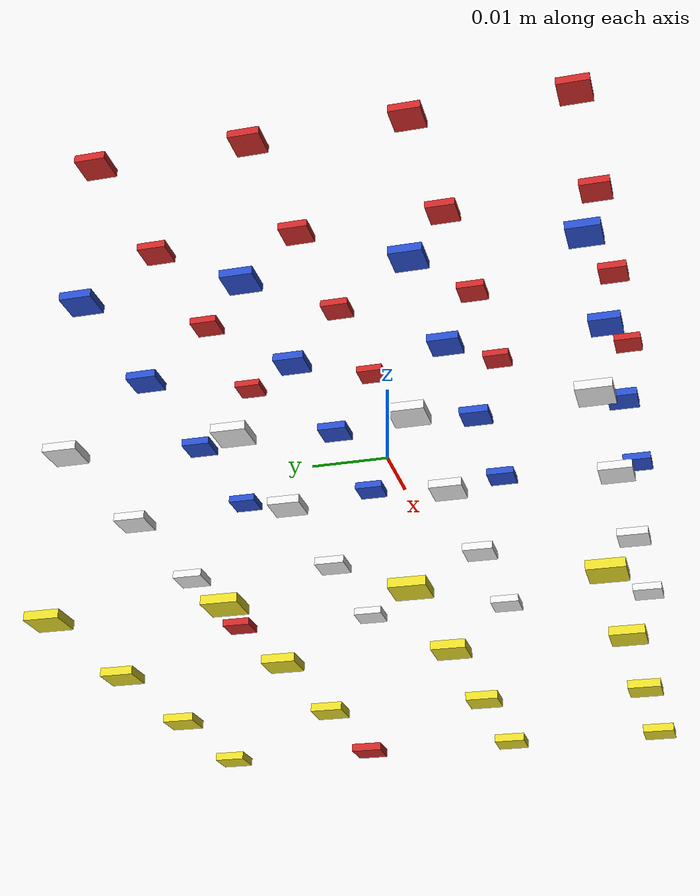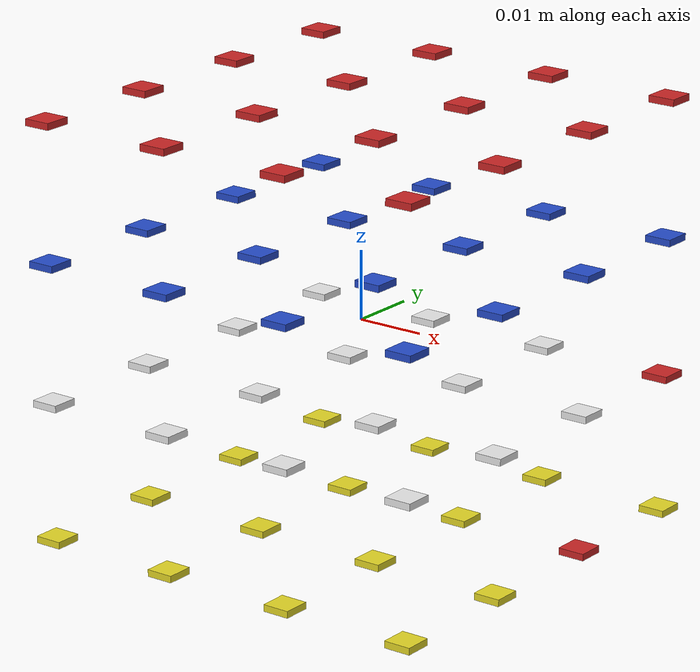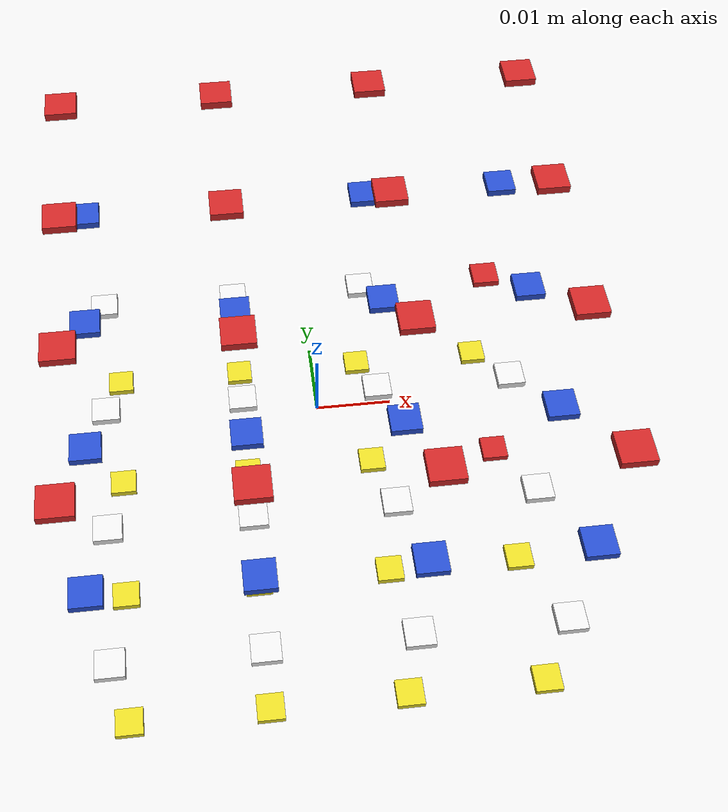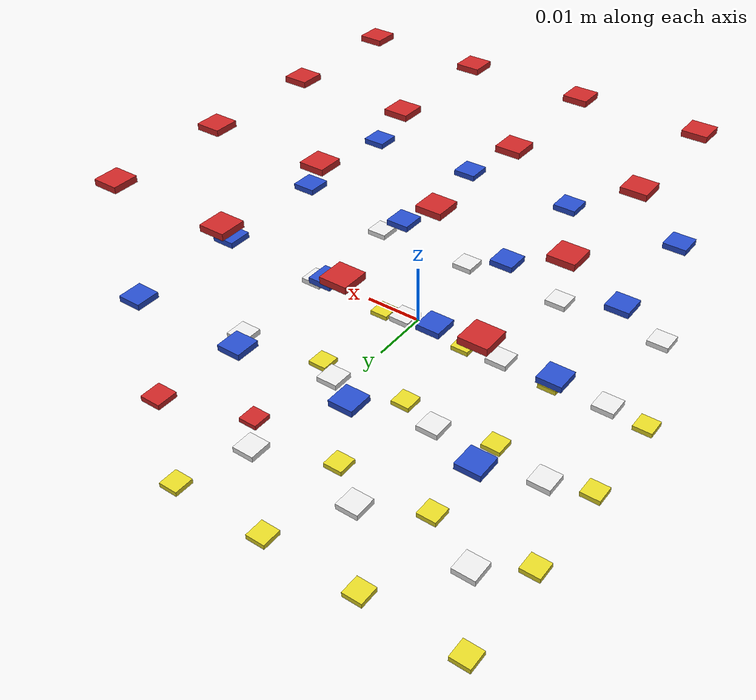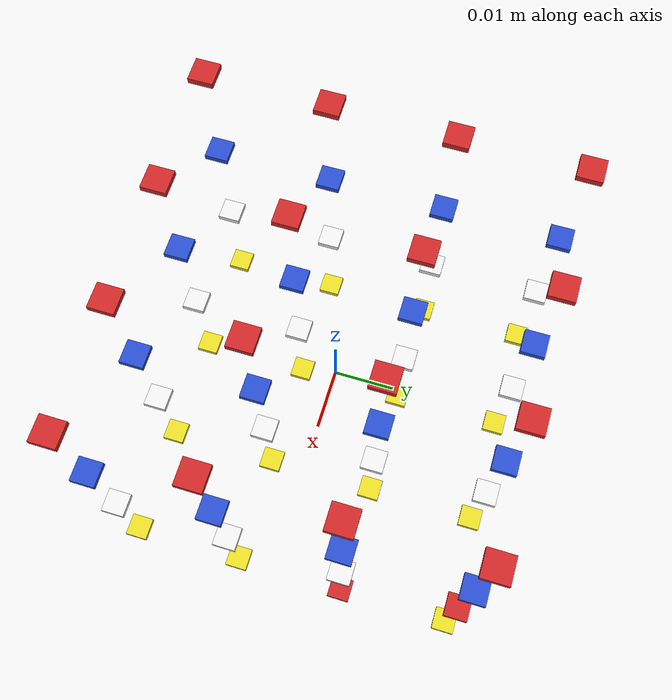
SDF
<?xml version="1.0" ?>
<sdf version='1.5'>
  <model name='imu_cube'>

<!-- 1st ----- top   4st ----- bottom -->

<!-- 1st layer  -->
    <include>
      <uri>model://MPU6050_0</uri>
      <pose>-0.03 0.03 0.03 0 0 0</pose>
    </include>
    <joint name="6050_0_joint" type="fixed">
      <child>6050_0::link</child>
      <parent>iris::base_link</parent>
    </joint>

    <include>
      <uri>model://MPU6050_1</uri>
      <pose>-0.01 0.03 0.03 0 0 0</pose>
    </include>
    <joint name="6050_1_joint" type="fixed">
      <child>6050_1::link</child>
      <parent>iris::base_link</parent>
    </joint>

    <include>
      <uri>model://MPU6050_2</uri>
      <pose>0.01 0.03 0.03 0 0 0</pose>
    </include>
    <joint name="6050_2_joint" type="fixed">
      <child>6050_2::link</child>
      <parent>iris::base_link</parent>
    </joint>

    <include>
      <uri>model://MPU6050_3</uri>
      <pose>0.03 0.03 0.03 0 0 0</pose>
    </include>
    <joint name="6050_3_joint" type="fixed">
      <child>6050_3::link</child>
      <parent>iris::base_link</parent>
    </joint>

    <include>
      <uri>model://MPU6050_4</uri>
      <pose>-0.03 0.01 0.03 0 0 0</pose>
    </include>
    <joint name="6050_4_joint" type="fixed">
      <child>6050_4::link</child>
      <parent>iris::base_link</parent>
    </joint>

    <include>
      <uri>model://MPU6050_5</uri>
      <pose>-0.01 0.01 0.03 0 0 0</pose>
    </include>
    <joint name="6050_5_joint" type="fixed">
      <child>6050_5::link</child>
      <parent>iris::base_link</parent>
    </joint>

    <include>
      <uri>model://MPU6050_6</uri>
      <pose>0.01 0.01 0.03 0 0 0</pose>
    </include>
    <joint name="6050_6_joint" type="fixed">
      <child>6050_6::link</child>
      <parent>iris::base_link</parent>
    </joint>

    <include>
      <uri>model://MPU6050_7</uri>
      <pose>0.03 0.01 0.03 0 0 0</pose>
    </include>
    <joint name="6050_7_joint" type="fixed">
      <child>6050_7::link</child>
      <parent>iris::base_link</parent>
    </joint>

    <include>
      <uri>model://MPU6050_8</uri>
      <pose>-0.03 -0.01 0.03 0 0 0</pose>
    </include>
    <joint name="6050_8_joint" type="fixed">
      <child>6050_8::link</child>
      <parent>iris::base_link</parent>
    </joint>

    <include>
      <uri>model://MPU6050_9</uri>
      <pose>-0.01 -0.01 0.03 0 0 0</pose>
    </include>
    <joint name="6050_9_joint" type="fixed">
      <child>6050_9::link</child>
      <parent>iris::base_link</parent>
    </joint>

    <include>
      <uri>model://MPU6050_10</uri>
      <pose>0.01 -0.01 0.03 0 0 0</pose>
    </include>
    <joint name="6050_10_joint" type="fixed">
      <child>6050_10::link</child>
      <parent>iris::base_link</parent>
    </joint>

    <include>
      <uri>model://MPU6050_11</uri>
      <pose>0.03 -0.01 0.03 0 0 0</pose>
    </include>
    <joint name="6050_11_joint" type="fixed">
      <child>6050_11::link</child>
      <parent>iris::base_link</parent>
    </joint>

    <include>
      <uri>model://MPU6050_12</uri>
      <pose>-0.03 -0.03 0.03 0 0 0</pose>
    </include>
    <joint name="6050_12_joint" type="fixed">
      <child>6050_12::link</child>
      <parent>iris::base_link</parent>
    </joint>

    <include>
      <uri>model://MPU6050_13</uri>
      <pose>-0.01 -0.03 0.03 0 0 0</pose>
    </include>
    <joint name="6050_13_joint" type="fixed">
      <child>6050_13::link</child>
      <parent>iris::base_link</parent>
    </joint>

    <include>
      <uri>model://MPU6050_14</uri>
      <pose>0.01 -0.03 0.03 0 0 0</pose>
    </include>
    <joint name="6050_14_joint" type="fixed">
      <child>6050_14::link</child>
      <parent>iris::base_link</parent>
    </joint>

    <include>
      <uri>model://MPU6050_15</uri>
      <pose>0.03 -0.03 0.03 0 0 0</pose>
    </include>
    <joint name="6050_15_joint" type="fixed">
      <child>6050_15::link</child>
      <parent>iris::base_link</parent>
    </joint>

<!-- 2st layer -->

    <include>
      <uri>model://MPU6500_0</uri>
      <pose>-0.03 0.03 0.01 0 0 0</pose>
    </include>
    <joint name="6500_0_joint" type="fixed">
      <child>6500_0::link</child>
      <parent>iris::base_link</parent>
    </joint>

    <include>
      <uri>model://MPU6500_1</uri>
      <pose>-0.01 0.03 0.01 0 0 0</pose>
    </include>
    <joint name="6500_1_joint" type="fixed">
      <child>6500_1::link</child>
      <parent>iris::base_link</parent>
    </joint>

    <include>
      <uri>model://MPU6500_2</uri>
      <pose>0.01 0.03 0.01 0 0 0</pose>
    </include>
    <joint name="6500_2_joint" type="fixed">
      <child>6500_2::link</child>
      <parent>iris::base_link</parent>
    </joint>

    <include>
      <uri>model://MPU6500_3</uri>
      <pose>0.03 0.03 0.01 0 0 0</pose>
    </include>
    <joint name="6500_3_joint" type="fixed">
      <child>6500_3::link</child>
      <parent>iris::base_link</parent>
    </joint>

    <include>
      <uri>model://MPU6500_4</uri>
      <pose>-0.03 0.01 0.01 0 0 0</pose>
    </include>
    <joint name="6500_4_joint" type="fixed">
      <child>6500_4::link</child>
      <parent>iris::base_link</parent>
    </joint>

    <include>
      <uri>model://MPU6500_5</uri>
      <pose>-0.01 0.01 0.01 0 0 0</pose>
    </include>
    <joint name="6500_5_joint" type="fixed">
      <child>6500_5::link</child>
      <parent>iris::base_link</parent>
    </joint>

    <include>
      <uri>model://MPU6500_6</uri>
      <pose>0.01 0.01 0.01 0 0 0</pose>
    </include>
    <joint name="6500_6_joint" type="fixed">
      <child>6500_6::link</child>
      <parent>iris::base_link</parent>
    </joint>

    <include>
      <uri>model://MPU6500_7</uri>
      <pose>0.03 0.01 0.01 0 0 0</pose>
    </include>
    <joint name="6500_7_joint" type="fixed">
      <child>6500_7::link</child>
      <parent>iris::base_link</parent>
    </joint>

    <include>
      <uri>model://MPU6500_8</uri>
      <pose>-0.03 -0.01 0.01 0 0 0</pose>
    </include>
    <joint name="6500_8_joint" type="fixed">
      <child>6500_8::link</child>
      <parent>iris::base_link</parent>
    </joint>

    <include>
      <uri>model://MPU6500_9</uri>
      <pose>-0.01 -0.01 0.01 0 0 0</pose>
    </include>
    <joint name="6500_9_joint" type="fixed">
      <child>6500_9::link</child>
      <parent>iris::base_link</parent>
    </joint>

    <include>
      <uri>model://MPU6500_10</uri>
      <pose>0.01 -0.01 0.01 0 0 0</pose>
    </include>
    <joint name="6500_10_joint" type="fixed">
      <child>6500_10::link</child>
      <parent>iris::base_link</parent>
    </joint>

    <include>
      <uri>model://MPU6500_11</uri>
      <pose>0.03 -0.01 0.01 0 0 0</pose>
    </include>
    <joint name="6500_11_joint" type="fixed">
      <child>6500_11::link</child>
      <parent>iris::base_link</parent>
    </joint>

    <include>
      <uri>model://MPU6500_12</uri>
      <pose>-0.03 -0.03 0.01 0 0 0</pose>
    </include>
    <joint name="6500_12_joint" type="fixed">
      <child>6500_12::link</child>
      <parent>iris::base_link</parent>
    </joint>

    <include>
      <uri>model://MPU6500_13</uri>
      <pose>-0.01 -0.03 0.01 0 0 0</pose>
    </include>
    <joint name="6500_13_joint" type="fixed">
      <child>6500_13::link</child>
      <parent>iris::base_link</parent>
    </joint>

    <include>
      <uri>model://MPU6500_14</uri>
      <pose>0.01 -0.03 0.01 0 0 0</pose>
    </include>
    <joint name="6500_14_joint" type="fixed">
      <child>6500_14::link</child>
      <parent>iris::base_link</parent>
    </joint>

    <include>
      <uri>model://MPU6500_15</uri>
      <pose>0.03 -0.03 0.01 0 0 0</pose>
    </include>
    <joint name="6500_15_joint" type="fixed">
      <child>6500_15::link</child>
      <parent>iris::base_link</parent>
    </joint>

<!-- 3st layer -->

    <include>
      <uri>model://MPU9150_0</uri>
      <pose>-0.03 0.03 -0.01 0 0 0</pose>
    </include>
    <joint name="9150_0_joint" type="fixed">
      <child>9150_0::link</child>
      <parent>iris::base_link</parent>
    </joint>

    <include>
      <uri>model://MPU9150_1</uri>
      <pose>-0.01 0.03 -0.01 0 0 0</pose>
    </include>
    <joint name="9150_1_joint" type="fixed">
      <child>9150_1::link</child>
      <parent>iris::base_link</parent>
    </joint>

    <include>
      <uri>model://MPU9150_2</uri>
      <pose>0.01 0.03 -0.01 0 0 0</pose>
    </include>
    <joint name="9150_2_joint" type="fixed">
      <child>9150_2::link</child>
      <parent>iris::base_link</parent>
    </joint>

    <include>
      <uri>model://MPU9150_3</uri>
      <pose>0.03 0.03 -0.01 0 0 0</pose>
    </include>
    <joint name="9150_3_joint" type="fixed">
      <child>9150_3::link</child>
      <parent>iris::base_link</parent>
    </joint>

    <include>
      <uri>model://MPU9150_4</uri>
      <pose>-0.03 0.01 -0.01 0 0 0</pose>
    </include>
    <joint name="9150_4_joint" type="fixed">
      <child>9150_4::link</child>
      <parent>iris::base_link</parent>
    </joint>

    <include>
      <uri>model://MPU9150_5</uri>
      <pose>-0.01 0.01 -0.01 0 0 0</pose>
    </include>
    <joint name="9150_5_joint" type="fixed">
      <child>9150_5::link</child>
      <parent>iris::base_link</parent>
    </joint>

    <include>
      <uri>model://MPU9150_6</uri>
      <pose>0.01 0.01 -0.01 0 0 0</pose>
    </include>
    <joint name="9150_6_joint" type="fixed">
      <child>9150_6::link</child>
      <parent>iris::base_link</parent>
    </joint>

    <include>
      <uri>model://MPU9150_7</uri>
      <pose>0.03 0.01 -0.01 0 0 0</pose>
    </include>
    <joint name="9150_7_joint" type="fixed">
      <child>9150_7::link</child>
      <parent>iris::base_link</parent>
    </joint>

    <include>
      <uri>model://MPU9150_8</uri>
      <pose>-0.03 -0.01 -0.01 0 0 0</pose>
    </include>
    <joint name="9150_8_joint" type="fixed">
      <child>9150_8::link</child>
      <parent>iris::base_link</parent>
    </joint>

    <include>
      <uri>model://MPU9150_9</uri>
      <pose>-0.01 -0.01 -0.01 0 0 0</pose>
    </include>
    <joint name="9150_9_joint" type="fixed">
      <child>9150_9::link</child>
      <parent>iris::base_link</parent>
    </joint>

    <include>
      <uri>model://MPU9150_10</uri>
      <pose>0.01 -0.01 -0.01 0 0 0</pose>
    </include>
    <joint name="9150_10_joint" type="fixed">
      <child>9150_10::link</child>
      <parent>iris::base_link</parent>
    </joint>

    <include>
      <uri>model://MPU9150_11</uri>
      <pose>0.03 -0.01 -0.01 0 0 0</pose>
    </include>
    <joint name="9150_11_joint" type="fixed">
      <child>9150_11::link</child>
      <parent>iris::base_link</parent>
    </joint>

    <include>
      <uri>model://MPU9150_12</uri>
      <pose>-0.03 -0.03 -0.01 0 0 0</pose>
    </include>
    <joint name="9150_12_joint" type="fixed">
      <child>9150_12::link</child>
      <parent>iris::base_link</parent>
    </joint>

    <include>
      <uri>model://MPU9150_13</uri>
      <pose>-0.01 -0.03 -0.01 0 0 0</pose>
    </include>
    <joint name="9150_13_joint" type="fixed">
      <child>9150_13::link</child>
      <parent>iris::base_link</parent>
    </joint>

    <include>
      <uri>model://MPU9150_14</uri>
      <pose>0.01 -0.03 -0.01 0 0 0</pose>
    </include>
    <joint name="9150_14_joint" type="fixed">
      <child>9150_14::link</child>
      <parent>iris::base_link</parent>
    </joint>

    <include>
      <uri>model://MPU9150_15</uri>
      <pose>0.03 -0.03 -0.01 0 0 0</pose>
    </include>
    <joint name="9150_15_joint" type="fixed">
      <child>9150_15::link</child>
      <parent>iris::base_link</parent>
    </joint>

<!-- 4st layer -->

    <include>
      <uri>model://MPU9250_0</uri>
      <pose>-0.03 0.03 -0.03 0 0 0</pose>
    </include>
    <joint name="9250_0_joint" type="fixed">
      <child>9250_0::link</child>
      <parent>iris::base_link</parent>
    </joint>

    <include>
      <uri>model://MPU9250_1</uri>
      <pose>-0.01 0.03 -0.03 0 0 0</pose>
    </include>
    <joint name="9250_1_joint" type="fixed">
      <child>9250_1::link</child>
      <parent>iris::base_link</parent>
    </joint>

    <include>
      <uri>model://MPU9250_2</uri>
      <pose>0.01 0.03 -0.03 0 0 0</pose>
    </include>
    <joint name="9250_2_joint" type="fixed">
      <child>9250_2::link</child>
      <parent>iris::base_link</parent>
    </joint>

    <include>
      <uri>model://MPU9250_3</uri>
      <pose>0.03 0.03 -0.03 0 0 0</pose>
    </include>
    <joint name="9250_3_joint" type="fixed">
      <child>9250_3::link</child>
      <parent>iris::base_link</parent>
    </joint>

    <include>
      <uri>model://MPU9250_4</uri>
      <pose>-0.03 0.01 -0.03 0 0 0</pose>
    </include>
    <joint name="9250_4_joint" type="fixed">
      <child>9250_4::link</child>
      <parent>iris::base_link</parent>
    </joint>

    <include>
      <uri>model://MPU9250_5</uri>
      <pose>-0.01 0.01 -0.03 0 0 0</pose>
    </include>
    <joint name="9250_5_joint" type="fixed">
      <child>9250_5::link</child>
      <parent>iris::base_link</parent>
    </joint>

    <include>
      <uri>model://MPU9250_6</uri>
      <pose>0.01 0.01 -0.03 0 0 0</pose>
    </include>
    <joint name="9250_6_joint" type="fixed">
      <child>9250_6::link</child>
      <parent>iris::base_link</parent>
    </joint>

    <include>
      <uri>model://MPU9250_7</uri>
      <pose>0.03 0.01 -0.03 0 0 0</pose>
    </include>
    <joint name="9250_7_joint" type="fixed">
      <child>9250_7::link</child>
      <parent>iris::base_link</parent>
    </joint>

    <include>
      <uri>model://MPU9250_8</uri>
      <pose>-0.03 -0.01 -0.03 0 0 0</pose>
    </include>
    <joint name="9250_8_joint" type="fixed">
      <child>9250_8::link</child>
      <parent>iris::base_link</parent>
    </joint>

    <include>
      <uri>model://MPU9250_9</uri>
      <pose>-0.01 -0.01 -0.03 0 0 0</pose>
    </include>
    <joint name="9250_9_joint" type="fixed">
      <child>9250_9::link</child>
      <parent>iris::base_link</parent>
    </joint>

    <include>
      <uri>model://MPU9250_10</uri>
      <pose>0.01 -0.01 -0.03 0 0 0</pose>
    </include>
    <joint name="9250_10_joint" type="fixed">
      <child>9250_10::link</child>
      <parent>iris::base_link</parent>
    </joint>

    <include>
      <uri>model://MPU9250_11</uri>
      <pose>0.03 -0.01 -0.03 0 0 0</pose>
    </include>
    <joint name="9250_11_joint" type="fixed">
      <child>9250_11::link</child>
      <parent>iris::base_link</parent>
    </joint>

    <include>
      <uri>model://MPU9250_12</uri>
      <pose>-0.03 -0.03 -0.03 0 0 0</pose>
    </include>
    <joint name="9250_12_joint" type="fixed">
      <child>9250_12::link</child>
      <parent>iris::base_link</parent>
    </joint>

    <include>
      <uri>model://MPU9250_13</uri>
      <pose>-0.01 -0.03 -0.03 0 0 0</pose>
    </include>
    <joint name="9250_13_joint" type="fixed">
      <child>9250_13::link</child>
      <parent>iris::base_link</parent>
    </joint>

    <include>
      <uri>model://MPU9250_14</uri>
      <pose>0.01 -0.03 -0.03 0 0 0</pose>
    </include>
    <joint name="9250_14_joint" type="fixed">
      <child>9250_14::link</child>
      <parent>iris::base_link</parent>
    </joint>

    <include>
      <uri>model://MPU9250_15</uri>
      <pose>0.03 -0.03 -0.03 0 0 0</pose>
    </include>
    <joint name="9250_15_joint" type="fixed">
      <child>9250_15::link</child>
      <parent>iris::base_link</parent>
    </joint>

  </model>
</sdf>
<!-- vim: set noet fenc=utf-8 ff=unix sts=0 sw=4 ts=4 : -->

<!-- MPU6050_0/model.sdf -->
<sdf version="1.5">
  <model name="MPU6050_0">
    <link name="link">
      <inertial>
        <pose>0 0 0 0 0 0</pose>
        <mass>0.001</mass>
        <inertia>
          <ixx>1.67</ixx>
          <ixy>0</ixy>
          <ixz>0</ixz>
          <iyy>1.67</iyy>
          <iyz>0</iyz>
          <izz>1.67</izz>
        </inertia>
      </inertial>
      <visual name="visual">
        <pose>0 0 0 0 0 0</pose>
        <geometry>
          <box>
            <size>0.004 0.004 0.001</size>
          </box>
        </geometry>
	<material>
          <script>
            <name>Gazebo/Red</name>
            <uri>__default__</uri>
          </script>
        </material>
      </visual>
      <sensor name='IMU6050_0' type='imu'>
        <always_on>1</always_on>
        <update_rate>1000</update_rate>
        <visualize>1</visualize>
        <topic>__default_topic__</topic>
        <imu/>

	<pose>0 0 0 0 0 0</pose>
      </sensor>
    </link>
          <plugin name="imu_plugin" filename="libhector_gazebo_ros_imu.so">
            <updateRate>1000</updateRate>
            <bodyName>link</bodyName>
            <topicName>/mpu6050_0</topicName>
            <serviceName>/mpu6050_0/calibrate</serviceName>
            <accelOffset>0.0 0.0 0.0</accelOffset>
            <accelDrift>0.0 0.0 0.0</accelDrift>
            <accelDriftFrequency>0.0 0.0 0.0</accelDriftFrequency>
            <accelGaussianNoise>0.035 0.035 0.035</accelGaussianNoise>
            <rateOffset>0.0 0.0 0.0</rateOffset>
            <rateDrift>0.0 0.0 0.0</rateDrift>
            <rateDriftFrequency>0.0 0.0 0.0</rateDriftFrequency>
            <rateGaussianNoise>0.05 0.05 0.05</rateGaussianNoise>
            <headingOffset>0.0</headingOffset>
            <headingDrift>0.0</headingDrift>
            <headingDriftFrequency>0.0</headingDriftFrequency>
            <headingGaussianNoise>0.0</headingGaussianNoise>
            <rpyOffset>0.0 0.0 0.0</rpyOffset>
            <xyzOffset>0.0 0.0 0.0</xyzOffset>
            <gaussianNoise>0.0</gaussianNoise>
        </plugin>
  </model>
</sdf>

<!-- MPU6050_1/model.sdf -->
<sdf version="1.5">
  <model name="MPU6050_1">
    <link name="link">
      <inertial>
        <pose>0 0 0 0 0 0</pose>
        <mass>0.001</mass>
        <inertia>
          <ixx>1.67</ixx>
          <ixy>0</ixy>
          <ixz>0</ixz>
          <iyy>1.67</iyy>
          <iyz>0</iyz>
          <izz>1.67</izz>
        </inertia>
      </inertial>
      <visual name="visual">
        <pose>0 0 0 0 0 0</pose>
        <geometry>
          <box>
            <size>0.004 0.004 0.001</size>
          </box>
        </geometry>
	<material>
          <script>
            <name>Gazebo/Red</name>
            <uri>__default__</uri>
          </script>
        </material>
      </visual>
      <sensor name='IMU6050' type='imu'>
        <always_on>1</always_on>
        <update_rate>1000</update_rate>
        <visualize>1</visualize>
        <topic>__default_topic__</topic>
        <imu/>

	<pose>0 0 0 0 0 0</pose>
      </sensor>
    </link>
          <plugin name="imu_plugin" filename="libhector_gazebo_ros_imu.so">
            <updateRate>1000</updateRate>
            <bodyName>link</bodyName>
            <topicName>/mpu6050_1</topicName>
            <serviceName>/mpu6050_1/calibrate</serviceName>
            <accelOffset>0.0 0.0 0.0</accelOffset>
            <accelDrift>0.0 0.0 0.0</accelDrift>
            <accelDriftFrequency>0.0 0.0 0.0</accelDriftFrequency>
            <accelGaussianNoise>0.0351 0.0351 0.0351</accelGaussianNoise>
            <rateOffset>0.0 0.0 0.0</rateOffset>
            <rateDrift>0.0 0.0 0.0</rateDrift>
            <rateDriftFrequency>0.0 0.0 0.0</rateDriftFrequency>
            <rateGaussianNoise>0.0501 0.0501 0.0501</rateGaussianNoise>
            <headingOffset>0.0</headingOffset>
            <headingDrift>0.0</headingDrift>
            <headingDriftFrequency>0.0</headingDriftFrequency>
            <headingGaussianNoise>0.0</headingGaussianNoise>
            <rpyOffset>0.0 0.0 0.0</rpyOffset>
            <xyzOffset>0.0 0.0 0.0</xyzOffset>
            <gaussianNoise>0.0</gaussianNoise>
        </plugin>
  </model>
</sdf>

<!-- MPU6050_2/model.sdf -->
<sdf version="1.5">
  <model name="MPU6050_2">
    <link name="link">
      <inertial>
        <pose>0 0 0 0 0 0</pose>
        <mass>0.001</mass>
        <inertia>
          <ixx>1.67</ixx>
          <ixy>0</ixy>
          <ixz>0</ixz>
          <iyy>1.67</iyy>
          <iyz>0</iyz>
          <izz>1.67</izz>
        </inertia>
      </inertial>
      <visual name="visual">
        <pose>0 0 0 0 0 0</pose>
        <geometry>
          <box>
            <size>0.004 0.004 0.001</size>
          </box>
        </geometry>
	<material>
          <script>
            <name>Gazebo/Red</name>
            <uri>__default__</uri>
          </script>
        </material>
      </visual>
      <sensor name='IMU6050' type='imu'>
        <always_on>1</always_on>
        <update_rate>1000</update_rate>
        <visualize>1</visualize>
        <topic>__default_topic__</topic>
        <imu/>

	<pose>0 0 0 0 0 0</pose>
      </sensor>
    </link>
          <plugin name="imu_plugin" filename="libhector_gazebo_ros_imu.so">
            <updateRate>100</updateRate>
            <bodyName>link</bodyName>
            <topicName>/mpu6050_2</topicName>
            <serviceName>/mpu6050_2/calibrate</serviceName>
            <accelOffset>0.0 0.0 0.0</accelOffset>
            <accelDrift>0.0 0.0 0.0</accelDrift>
            <accelDriftFrequency>0.0 0.0 0.0</accelDriftFrequency>
            <accelGaussianNoise>0.0352 0.0352 0.0352</accelGaussianNoise>
            <rateOffset>0.0 0.0 0.0</rateOffset>
            <rateDrift>0.0 0.0 0.0</rateDrift>
            <rateDriftFrequency>0.0 0.0 0.0</rateDriftFrequency>
            <rateGaussianNoise>0.0502 0.0502 0.0502</rateGaussianNoise>
            <headingOffset>0.0</headingOffset>
            <headingDrift>0.0</headingDrift>
            <headingDriftFrequency>0.0</headingDriftFrequency>
            <headingGaussianNoise>0.0</headingGaussianNoise>
            <rpyOffset>0.0 0.0 0.0</rpyOffset>
            <xyzOffset>0.0 0.0 0.0</xyzOffset>
            <gaussianNoise>0.0</gaussianNoise>
        </plugin>
  </model>
</sdf>

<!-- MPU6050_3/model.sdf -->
<sdf version="1.5">
  <model name="MPU6050_3">
    <link name="link">
      <inertial>
        <pose>0 0 0 0 0 0</pose>
        <mass>0.001</mass>
        <inertia>
          <ixx>1.67</ixx>
          <ixy>0</ixy>
          <ixz>0</ixz>
          <iyy>1.67</iyy>
          <iyz>0</iyz>
          <izz>1.67</izz>
        </inertia>
      </inertial>
      <visual name="visual">
        <pose>0 0 0 0 0 0</pose>
        <geometry>
          <box>
            <size>0.004 0.004 0.001</size>
          </box>
        </geometry>
	<material>
          <script>
            <name>Gazebo/Red</name>
            <uri>__default__</uri>
          </script>
        </material>
      </visual>
      <sensor name='IMU6050' type='imu'>
        <always_on>1</always_on>
        <update_rate>1000</update_rate>
        <visualize>1</visualize>
        <topic>__default_topic__</topic>
        <imu/>

	<pose>0 0 0 0 0 0</pose>
      </sensor>
    </link>
          <plugin name="imu_plugin" filename="libhector_gazebo_ros_imu.so">
            <updateRate>100</updateRate>
            <bodyName>link</bodyName>
            <topicName>/mpu6050_3</topicName>
            <serviceName>/mpu6050_3/calibrate</serviceName>
            <accelOffset>0.0 0.0 0.0</accelOffset>
            <accelDrift>0.0 0.0 0.0</accelDrift>
            <accelDriftFrequency>0.0353 0.0353 0.0353</accelDriftFrequency>
            <accelGaussianNoise>0.0 0.0 0.0</accelGaussianNoise>
            <rateOffset>0.0 0.0 0.0</rateOffset>
            <rateDrift>0.0 0.0 0.0</rateDrift>
            <rateDriftFrequency>0.0 0.0 0.0</rateDriftFrequency>
            <rateGaussianNoise>0.0503 0.0503 0.0503</rateGaussianNoise>
            <headingOffset>0.0</headingOffset>
            <headingDrift>0.0</headingDrift>
            <headingDriftFrequency>0.0</headingDriftFrequency>
            <headingGaussianNoise>0.0</headingGaussianNoise>
            <rpyOffset>0.0 0.0 0.0</rpyOffset>
            <xyzOffset>0.0 0.0 0.0</xyzOffset>
            <gaussianNoise>0.0</gaussianNoise>
        </plugin>
  </model>
</sdf>

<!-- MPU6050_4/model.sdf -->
<sdf version="1.5">
  <model name="MPU6050_4">
    <link name="link">
      <inertial>
        <pose>0 0 0 0 0 0</pose>
        <mass>0.001</mass>
        <inertia>
          <ixx>1.67</ixx>
          <ixy>0</ixy>
          <ixz>0</ixz>
          <iyy>1.67</iyy>
          <iyz>0</iyz>
          <izz>1.67</izz>
        </inertia>
      </inertial>
      <visual name="visual">
        <pose>0 0 0 0 0 0</pose>
        <geometry>
          <box>
            <size>0.004 0.004 0.001</size>
          </box>
        </geometry>
	<material>
          <script>
            <name>Gazebo/Red</name>
            <uri>__default__</uri>
          </script>
        </material>
      </visual>
      <sensor name='IMU6050' type='imu'>
        <always_on>1</always_on>
        <update_rate>1000</update_rate>
        <visualize>1</visualize>
        <topic>__default_topic__</topic>
        <imu/>

	<pose>0 0 0 0 0 0</pose>
      </sensor>
    </link>
          <plugin name="imu_plugin" filename="libhector_gazebo_ros_imu.so">
            <updateRate>100</updateRate>
            <bodyName>link</bodyName>
            <topicName>/mpu6050_4</topicName>
            <serviceName>/mpu6050_4/calibrate</serviceName>
            <accelOffset>0.0 0.0 0.0</accelOffset>
            <accelDrift>0.0 0.0 0.0</accelDrift>
            <accelDriftFrequency>0.0 0.0 0.0</accelDriftFrequency>
            <accelGaussianNoise>0.0354 0.0354 0.0354</accelGaussianNoise>
            <rateOffset>0.0 0.0 0.0</rateOffset>
            <rateDrift>0.0 0.0 0.0</rateDrift>
            <rateDriftFrequency>0.0 0.0 0.0</rateDriftFrequency>
            <rateGaussianNoise>0.0504 0.0504 0.0504</rateGaussianNoise>
            <headingOffset>0.0</headingOffset>
            <headingDrift>0.0</headingDrift>
            <headingDriftFrequency>0.0</headingDriftFrequency>
            <headingGaussianNoise>0.0</headingGaussianNoise>
            <rpyOffset>0.0 0.0 0.0</rpyOffset>
            <xyzOffset>0.0 0.0 0.0</xyzOffset>
            <gaussianNoise>0.0</gaussianNoise>
        </plugin>
  </model>
</sdf>

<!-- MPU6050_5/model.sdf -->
<sdf version="1.5">
  <model name="MPU6050_5">
    <link name="link">
      <inertial>
        <pose>0 0 0 0 0 0</pose>
        <mass>0.001</mass>
        <inertia>
          <ixx>1.67</ixx>
          <ixy>0</ixy>
          <ixz>0</ixz>
          <iyy>1.67</iyy>
          <iyz>0</iyz>
          <izz>1.67</izz>
        </inertia>
      </inertial>
      <visual name="visual">
        <pose>0 0 0 0 0 0</pose>
        <geometry>
          <box>
            <size>0.004 0.004 0.001</size>
          </box>
        </geometry>
	<material>
          <script>
            <name>Gazebo/Red</name>
            <uri>__default__</uri>
          </script>
        </material>
      </visual>
      <sensor name='IMU6050_5' type='imu'>
        <always_on>1</always_on>
        <update_rate>1000</update_rate>
        <visualize>1</visualize>
        <topic>__default_topic__</topic>
        <imu/>

	<pose>0 0 0 0 0 0</pose>
      </sensor>
    </link>
          <plugin name="imu_plugin" filename="libhector_gazebo_ros_imu.so">
            <updateRate>100</updateRate>
            <bodyName>link</bodyName>
            <topicName>/mpu6050_5</topicName>
            <serviceName>/mpu6050_5/calibrate</serviceName>
            <accelOffset>0.0 0.0 0.0</accelOffset>
            <accelDrift>0.0 0.0 0.0</accelDrift>
            <accelDriftFrequency>0.0 0.0 0.0</accelDriftFrequency>
            <accelGaussianNoise>0.0355 0.0355 0.0355</accelGaussianNoise>
            <rateOffset>0.0 0.0 0.0</rateOffset>
            <rateDrift>0.0 0.0 0.0</rateDrift>
            <rateDriftFrequency>0.0 0.0 0.0</rateDriftFrequency>
            <rateGaussianNoise>0.0505 0.0505 0.0505</rateGaussianNoise>
            <headingOffset>0.0</headingOffset>
            <headingDrift>0.0</headingDrift>
            <headingDriftFrequency>0.0</headingDriftFrequency>
            <headingGaussianNoise>0.0</headingGaussianNoise>
            <rpyOffset>0.0 0.0 0.0</rpyOffset>
            <xyzOffset>0.0 0.0 0.0</xyzOffset>
            <gaussianNoise>0.0</gaussianNoise>
        </plugin>
  </model>
</sdf>

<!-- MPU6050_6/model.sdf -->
<sdf version="1.5">
  <model name="MPU6050_6">
    <link name="link">
      <inertial>
        <pose>0 0 0 0 0 0</pose>
        <mass>0.001</mass>
        <inertia>
          <ixx>1.67</ixx>
          <ixy>0</ixy>
          <ixz>0</ixz>
          <iyy>1.67</iyy>
          <iyz>0</iyz>
          <izz>1.67</izz>
        </inertia>
      </inertial>
      <visual name="visual">
        <pose>0 0 0 0 0 0</pose>
        <geometry>
          <box>
            <size>0.004 0.004 0.001</size>
          </box>
        </geometry>
	<material>
          <script>
            <name>Gazebo/Red</name>
            <uri>__default__</uri>
          </script>
        </material>
      </visual>
      <sensor name='IMU6050_6' type='imu'>
        <always_on>1</always_on>
        <update_rate>1000</update_rate>
        <visualize>1</visualize>
        <topic>__default_topic__</topic>
        <imu/>

	<pose>0 0 0 0 0 0</pose>
      </sensor>
    </link>
          <plugin name="imu_plugin" filename="libhector_gazebo_ros_imu.so">
            <updateRate>100</updateRate>
            <bodyName>link</bodyName>
            <topicName>/mpu6050_6</topicName>
            <serviceName>/mpu6050_6/calibrate</serviceName>
            <accelOffset>0.0 0.0 0.0</accelOffset>
            <accelDrift>0.0 0.0 0.0</accelDrift>
            <accelDriftFrequency>0.0 0.0 0.0</accelDriftFrequency>
            <accelGaussianNoise>0.0356 0.0356 0.0356</accelGaussianNoise>
            <rateOffset>0.0 0.0 0.0</rateOffset>
            <rateDrift>0.0 0.0 0.0</rateDrift>
            <rateDriftFrequency>0.0 0.0 0.0</rateDriftFrequency>
            <rateGaussianNoise>0.0506 0.0506 0.0506</rateGaussianNoise>
            <headingOffset>0.0</headingOffset>
            <headingDrift>0.0</headingDrift>
            <headingDriftFrequency>0.0</headingDriftFrequency>
            <headingGaussianNoise>0.0</headingGaussianNoise>
            <rpyOffset>0.0 0.0 0.0</rpyOffset>
            <xyzOffset>0.0 0.0 0.0</xyzOffset>
            <gaussianNoise>0.0</gaussianNoise>
        </plugin>
  </model>
</sdf>

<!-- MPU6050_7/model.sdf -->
<sdf version="1.5">
  <model name="MPU6050_7">
    <link name="link">
      <inertial>
        <pose>0 0 0 0 0 0</pose>
        <mass>0.001</mass>
        <inertia>
          <ixx>1.67</ixx>
          <ixy>0</ixy>
          <ixz>0</ixz>
          <iyy>1.67</iyy>
          <iyz>0</iyz>
          <izz>1.67</izz>
        </inertia>
      </inertial>
      <visual name="visual">
        <pose>0 0 0 0 0 0</pose>
        <geometry>
          <box>
            <size>0.004 0.004 0.001</size>
          </box>
        </geometry>
	<material>
          <script>
            <name>Gazebo/Red</name>
            <uri>__default__</uri>
          </script>
        </material>
      </visual>
      <sensor name='IMU6050_7' type='imu'>
        <always_on>1</always_on>
        <update_rate>1000</update_rate>
        <visualize>1</visualize>
        <topic>__default_topic__</topic>
        <imu/>

	<pose>0 0 0 0 0 0</pose>
      </sensor>
    </link>
          <plugin name="imu_plugin" filename="libhector_gazebo_ros_imu.so">
            <updateRate>100</updateRate>
            <bodyName>link</bodyName>
            <topicName>/mpu6050_7</topicName>
            <serviceName>/mpu6050_7/calibrate</serviceName>
            <accelOffset>0.0 0.0 0.0</accelOffset>
            <accelDrift>0.0 0.0 0.0</accelDrift>
            <accelDriftFrequency>0.0 0.0 0.0</accelDriftFrequency>
            <accelGaussianNoise>0.0357 0.0357 0.0357</accelGaussianNoise>
            <rateOffset>0.0 0.0 0.0</rateOffset>
            <rateDrift>0.0 0.0 0.0</rateDrift>
            <rateDriftFrequency>0.0 0.0 0.0</rateDriftFrequency>
            <rateGaussianNoise>0.0507 0.0507 0.0507</rateGaussianNoise>
            <headingOffset>0.0</headingOffset>
            <headingDrift>0.0</headingDrift>
            <headingDriftFrequency>0.0</headingDriftFrequency>
            <headingGaussianNoise>0.0</headingGaussianNoise>
            <rpyOffset>0.0 0.0 0.0</rpyOffset>
            <xyzOffset>0.0 0.0 0.0</xyzOffset>
            <gaussianNoise>0.0</gaussianNoise>
        </plugin>
  </model>
</sdf>

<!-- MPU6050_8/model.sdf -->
<sdf version="1.5">
  <model name="MPU6050_8">
    <link name="link">
      <inertial>
        <pose>0 0 0 0 0 0</pose>
        <mass>0.001</mass>
        <inertia>
          <ixx>1.67</ixx>
          <ixy>0</ixy>
          <ixz>0</ixz>
          <iyy>1.67</iyy>
          <iyz>0</iyz>
          <izz>1.67</izz>
        </inertia>
      </inertial>
      <visual name="visual">
        <pose>0 0 0 0 0 0</pose>
        <geometry>
          <box>
            <size>0.004 0.004 0.001</size>
          </box>
        </geometry>
	<material>
          <script>
            <name>Gazebo/Red</name>
            <uri>__default__</uri>
          </script>
        </material>
      </visual>
      <sensor name='IMU6050' type='imu'>
        <always_on>1</always_on>
        <update_rate>1000</update_rate>
        <visualize>1</visualize>
        <topic>__default_topic__</topic>
        <imu/>

	<pose>0 0 0 0 0 0</pose>
      </sensor>
    </link>
          <plugin name="imu_plugin" filename="libhector_gazebo_ros_imu.so">
            <updateRate>100</updateRate>
            <bodyName>link</bodyName>
            <topicName>/mpu6050_8</topicName>
            <serviceName>/mpu6050_8/calibrate</serviceName>
            <accelOffset>0.0 0.0 0.0</accelOffset>
            <accelDrift>0.0 0.0 0.0</accelDrift>
            <accelDriftFrequency>0.0 0.0 0.0</accelDriftFrequency>
            <accelGaussianNoise>0.0341 0.0341 0.0341</accelGaussianNoise>
            <rateOffset>0.0 0.0 0.0</rateOffset>
            <rateDrift>0.0 0.0 0.0</rateDrift>
            <rateDriftFrequency>0.0 0.0 0.0</rateDriftFrequency>
            <rateGaussianNoise>0.0491 0.0491 0.0491</rateGaussianNoise>
            <headingOffset>0.0</headingOffset>
            <headingDrift>0.0</headingDrift>
            <headingDriftFrequency>0.0</headingDriftFrequency>
            <headingGaussianNoise>0.0</headingGaussianNoise>
            <rpyOffset>0.0 0.0 0.0</rpyOffset>
            <xyzOffset>0.0 0.0 0.0</xyzOffset>
            <gaussianNoise>0.0</gaussianNoise>
        </plugin>
  </model>
</sdf>

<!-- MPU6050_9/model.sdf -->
<sdf version="1.5">
  <model name="MPU6050_9">
    <link name="link">
      <inertial>
        <pose>0 0 0 0 0 0</pose>
        <mass>0.001</mass>
        <inertia>
          <ixx>1.67</ixx>
          <ixy>0</ixy>
          <ixz>0</ixz>
          <iyy>1.67</iyy>
          <iyz>0</iyz>
          <izz>1.67</izz>
        </inertia>
      </inertial>
      <visual name="visual">
        <pose>0 0 0 0 0 0</pose>
        <geometry>
          <box>
            <size>0.004 0.004 0.001</size>
          </box>
        </geometry>
	<material>
          <script>
            <name>Gazebo/Red</name>
            <uri>__default__</uri>
          </script>
        </material>
      </visual>
      <sensor name='IMU6050' type='imu'>
        <always_on>1</always_on>
        <update_rate>1000</update_rate>
        <visualize>1</visualize>
        <topic>__default_topic__</topic>
        <imu/>

	<pose>0 0 0 0 0 0</pose>
      </sensor>
    </link>
          <plugin name="imu_plugin" filename="libhector_gazebo_ros_imu.so">
            <updateRate>100</updateRate>
            <bodyName>link</bodyName>
            <topicName>/mpu6050_9</topicName>
            <serviceName>/mpu6050_9/calibrate</serviceName>
            <accelOffset>0.0 0.0 0.0</accelOffset>
            <accelDrift>0.0 0.0 0.0</accelDrift>
            <accelDriftFrequency>0.0 0.0 0.0</accelDriftFrequency>
            <accelGaussianNoise>0.0342 0.0342 0.0342</accelGaussianNoise>
            <rateOffset>0.0 0.0 0.0</rateOffset>
            <rateDrift>0.0 0.0 0.0</rateDrift>
            <rateDriftFrequency>0.0 0.0 0.0</rateDriftFrequency>
            <rateGaussianNoise>0.0492 0.0492 0.0492</rateGaussianNoise>
            <headingOffset>0.0</headingOffset>
            <headingDrift>0.0</headingDrift>
            <headingDriftFrequency>0.0</headingDriftFrequency>
            <headingGaussianNoise>0.0</headingGaussianNoise>
            <rpyOffset>0.0 0.0 0.0</rpyOffset>
            <xyzOffset>0.0 0.0 0.0</xyzOffset>
            <gaussianNoise>0.0</gaussianNoise>
        </plugin>
  </model>
</sdf>

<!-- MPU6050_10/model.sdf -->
<sdf version="1.5">
  <model name="MPU6050_10">
    <link name="link">
      <inertial>
        <pose>0 0 0 0 0 0</pose>
        <mass>0.001</mass>
        <inertia>
          <ixx>1.67</ixx>
          <ixy>0</ixy>
          <ixz>0</ixz>
          <iyy>1.67</iyy>
          <iyz>0</iyz>
          <izz>1.67</izz>
        </inertia>
      </inertial>
      <visual name="visual">
        <pose>0 0 0 0 0 0</pose>
        <geometry>
          <box>
            <size>0.004 0.004 0.001</size>
          </box>
        </geometry>
	<material>
          <script>
            <name>Gazebo/Red</name>
            <uri>__default__</uri>
          </script>
        </material>
      </visual>
      <sensor name='IMU6050' type='imu'>
        <always_on>1</always_on>
        <update_rate>1000</update_rate>
        <visualize>1</visualize>
        <topic>__default_topic__</topic>
        <imu/>

	<pose>0 0 0 0 0 0</pose>
      </sensor>
    </link>
          <plugin name="imu_plugin" filename="libhector_gazebo_ros_imu.so">
            <updateRate>1000</updateRate>
            <bodyName>link</bodyName>
            <topicName>/mpu6050_10</topicName>
            <serviceName>/mpu6050_10/calibrate</serviceName>
            <accelOffset>0.0 0.0 0.0</accelOffset>
            <accelDrift>0.0 0.0 0.0</accelDrift>
            <accelDriftFrequency>0.0 0.0 0.0</accelDriftFrequency>
            <accelGaussianNoise>0.0343 0.0343 0.0344</accelGaussianNoise>
            <rateOffset>0.0 0.0 0.0</rateOffset>
            <rateDrift>0.0 0.0 0.0</rateDrift>
            <rateDriftFrequency>0.0 0.0 0.0</rateDriftFrequency>
            <rateGaussianNoise>0.0493 0.0493 0.0493</rateGaussianNoise>
            <headingOffset>0.0</headingOffset>
            <headingDrift>0.0</headingDrift>
            <headingDriftFrequency>0.0</headingDriftFrequency>
            <headingGaussianNoise>0.0</headingGaussianNoise>
            <rpyOffset>0.0 0.0 0.0</rpyOffset>
            <xyzOffset>0.0 0.0 0.0</xyzOffset>
            <gaussianNoise>0.0</gaussianNoise>
        </plugin>
  </model>
</sdf>

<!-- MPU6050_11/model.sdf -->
<sdf version="1.5">
  <model name="MPU6050_2">
    <link name="link">
      <inertial>
        <pose>0 0 0 0 0 0</pose>
        <mass>0.001</mass>
        <inertia>
          <ixx>1.67</ixx>
          <ixy>0</ixy>
          <ixz>0</ixz>
          <iyy>1.67</iyy>
          <iyz>0</iyz>
          <izz>1.67</izz>
        </inertia>
      </inertial>
      <visual name="visual">
        <pose>0 0 0 0 0 0</pose>
        <geometry>
          <box>
            <size>0.004 0.004 0.001</size>
          </box>
        </geometry>
	<material>
          <script>
            <name>Gazebo/Red</name>
            <uri>__default__</uri>
          </script>
        </material>
      </visual>
      <sensor name='IMU6050' type='imu'>
        <always_on>1</always_on>
        <update_rate>1000</update_rate>
        <visualize>1</visualize>
        <topic>__default_topic__</topic>
        <imu/>

	<pose>0 0 0 0 0 0</pose>
      </sensor>
    </link>
          <plugin name="imu_plugin" filename="libhector_gazebo_ros_imu.so">
            <updateRate>1000</updateRate>
            <bodyName>link</bodyName>
            <topicName>/mpu6050_11</topicName>
            <serviceName>/mpu6050_11/calibrate</serviceName>
            <accelOffset>0.0 0.0 0.0</accelOffset>
            <accelDrift>0.0 0.0 0.0</accelDrift>
            <accelDriftFrequency>0.0 0.0 0.0</accelDriftFrequency>
            <accelGaussianNoise>0.0344 0.0344 0.0344</accelGaussianNoise>
            <rateOffset>0.0 0.0 0.0</rateOffset>
            <rateDrift>0.0 0.0 0.0</rateDrift>
            <rateDriftFrequency>0.0 0.0 0.0</rateDriftFrequency>
            <rateGaussianNoise>0.0494 0.0494 0.0494</rateGaussianNoise>
            <headingOffset>0.0</headingOffset>
            <headingDrift>0.0</headingDrift>
            <headingDriftFrequency>0.0</headingDriftFrequency>
            <headingGaussianNoise>0.0</headingGaussianNoise>
            <rpyOffset>0.0 0.0 0.0</rpyOffset>
            <xyzOffset>0.0 0.0 0.0</xyzOffset>
            <gaussianNoise>0.0</gaussianNoise>
        </plugin>
  </model>
</sdf>

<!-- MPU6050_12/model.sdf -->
<sdf version="1.5">
  <model name="MPU6050_12">
    <link name="link">
      <inertial>
        <pose>0 0 0 0 0 0</pose>
        <mass>0.001</mass>
        <inertia>
          <ixx>1.67</ixx>
          <ixy>0</ixy>
          <ixz>0</ixz>
          <iyy>1.67</iyy>
          <iyz>0</iyz>
          <izz>1.67</izz>
        </inertia>
      </inertial>
      <visual name="visual">
        <pose>0 0 0 0 0 0</pose>
        <geometry>
          <box>
            <size>0.004 0.004 0.001</size>
          </box>
        </geometry>
	<material>
          <script>
            <name>Gazebo/Red</name>
            <uri>__default__</uri>
          </script>
        </material>
      </visual>
      <sensor name='IMU6050' type='imu'>
        <always_on>1</always_on>
        <update_rate>1000</update_rate>
        <visualize>1</visualize>
        <topic>__default_topic__</topic>
        <imu/>

	<pose>0 0 0 0 0 0</pose>
      </sensor>
    </link>
          <plugin name="imu_plugin" filename="libhector_gazebo_ros_imu.so">
            <updateRate>1000</updateRate>
            <bodyName>link</bodyName>
            <topicName>/mpu6050_12</topicName>
            <serviceName>/mpu6050_12/calibrate</serviceName>
            <accelOffset>0.0 0.0 0.0</accelOffset>
            <accelDrift>0.0 0.0 0.0</accelDrift>
            <accelDriftFrequency>0.0 0.0 0.0</accelDriftFrequency>
            <accelGaussianNoise>0.0345 0.0345 0.0345</accelGaussianNoise>
            <rateOffset>0.0 0.0 0.0</rateOffset>
            <rateDrift>0.0 0.0 0.0</rateDrift>
            <rateDriftFrequency>0.0 0.0 0.0</rateDriftFrequency>
            <rateGaussianNoise>0.0495 0.0495 0.0495</rateGaussianNoise>
            <headingOffset>0.0</headingOffset>
            <headingDrift>0.0</headingDrift>
            <headingDriftFrequency>0.0</headingDriftFrequency>
            <headingGaussianNoise>0.0</headingGaussianNoise>
            <rpyOffset>0.0 0.0 0.0</rpyOffset>
            <xyzOffset>0.0 0.0 0.0</xyzOffset>
            <gaussianNoise>0.0</gaussianNoise>
        </plugin>
  </model>
</sdf>

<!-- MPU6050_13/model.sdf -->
<sdf version="1.5">
  <model name="MPU6050_13">
    <link name="link">
      <inertial>
        <pose>0 0 0 0 0 0</pose>
        <mass>0.001</mass>
        <inertia>
          <ixx>1.67</ixx>
          <ixy>0</ixy>
          <ixz>0</ixz>
          <iyy>1.67</iyy>
          <iyz>0</iyz>
          <izz>1.67</izz>
        </inertia>
      </inertial>
      <visual name="visual">
        <pose>0 0 0 0 0 0</pose>
        <geometry>
          <box>
            <size>0.004 0.004 0.001</size>
          </box>
        </geometry>
	<material>
          <script>
            <name>Gazebo/Red</name>
            <uri>__default__</uri>
          </script>
        </material>
      </visual>
      <sensor name='IMU6050' type='imu'>
        <always_on>1</always_on>
        <update_rate>1000</update_rate>
        <visualize>1</visualize>
        <topic>__default_topic__</topic>
        <imu/>

	<pose>0 0 0 0 0 0</pose>
      </sensor>
    </link>
          <plugin name="imu_plugin" filename="libhector_gazebo_ros_imu.so">
            <updateRate>1000</updateRate>
            <bodyName>link</bodyName>
            <topicName>/mpu6050_13</topicName>
            <serviceName>/mpu6050_13/calibrate</serviceName>
            <accelOffset>0.0 0.0 0.0</accelOffset>
            <accelDrift>0.0 0.0 0.0</accelDrift>
            <accelDriftFrequency>0.0 0.0 0.0</accelDriftFrequency>
            <accelGaussianNoise>0.0346 0.0346 0.0346</accelGaussianNoise>
            <rateOffset>0.0 0.0 0.0</rateOffset>
            <rateDrift>0.0 0.0 0.0</rateDrift>
            <rateDriftFrequency>0.0 0.0 0.0</rateDriftFrequency>
            <rateGaussianNoise>0.0496 0.0496 0.0496</rateGaussianNoise>
            <headingOffset>0.0</headingOffset>
            <headingDrift>0.0</headingDrift>
            <headingDriftFrequency>0.0</headingDriftFrequency>
            <headingGaussianNoise>0.0</headingGaussianNoise>
            <rpyOffset>0.0 0.0 0.0</rpyOffset>
            <xyzOffset>0.0 0.0 0.0</xyzOffset>
            <gaussianNoise>0.0</gaussianNoise>
        </plugin>
  </model>
</sdf>

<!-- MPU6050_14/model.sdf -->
<sdf version="1.5">
  <model name="MPU6050_14">
    <link name="link">
      <inertial>
        <pose>0 0 0 0 0 0</pose>
        <mass>0.001</mass>
        <inertia>
          <ixx>1.67</ixx>
          <ixy>0</ixy>
          <ixz>0</ixz>
          <iyy>1.67</iyy>
          <iyz>0</iyz>
          <izz>1.67</izz>
        </inertia>
      </inertial>
      <visual name="visual">
        <pose>0 0 0 0 0 0</pose>
        <geometry>
          <box>
            <size>0.004 0.004 0.001</size>
          </box>
        </geometry>
	<material>
          <script>
            <name>Gazebo/Red</name>
            <uri>__default__</uri>
          </script>
        </material>
      </visual>
      <sensor name='IMU6050' type='imu'>
        <always_on>1</always_on>
        <update_rate>1000</update_rate>
        <visualize>1</visualize>
        <topic>__default_topic__</topic>
        <imu/>

	<pose>0 0 0 0 0 0</pose>
      </sensor>
    </link>
          <plugin name="imu_plugin" filename="libhector_gazebo_ros_imu.so">
            <updateRate>1000</updateRate>
            <bodyName>link</bodyName>
            <topicName>/mpu6050_14</topicName>
            <serviceName>/mpu6050_14/calibrate</serviceName>
            <accelOffset>0.0 0.0 0.0</accelOffset>
            <accelDrift>0.0 0.0 0.0</accelDrift>
            <accelDriftFrequency>0.0 0.0 0.0</accelDriftFrequency>
            <accelGaussianNoise>0.0347 0.0347 0.0347</accelGaussianNoise>
            <rateOffset>0.0 0.0 0.0</rateOffset>
            <rateDrift>0.0 0.0 0.0</rateDrift>
            <rateDriftFrequency>0.0 0.0 0.0</rateDriftFrequency>
            <rateGaussianNoise>0.0497 0.0497 0.0497</rateGaussianNoise>
            <headingOffset>0.0</headingOffset>
            <headingDrift>0.0</headingDrift>
            <headingDriftFrequency>0.0</headingDriftFrequency>
            <headingGaussianNoise>0.0</headingGaussianNoise>
            <rpyOffset>0.0 0.0 0.0</rpyOffset>
            <xyzOffset>0.0 0.0 0.0</xyzOffset>
            <gaussianNoise>0.0</gaussianNoise>
        </plugin>
  </model>
</sdf>

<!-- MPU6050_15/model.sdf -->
<sdf version="1.5">
  <model name="MPU6050_15">
    <link name="link">
      <inertial>
        <pose>0 0 0 0 0 0</pose>
        <mass>0.001</mass>
        <inertia>
          <ixx>1.67</ixx>
          <ixy>0</ixy>
          <ixz>0</ixz>
          <iyy>1.67</iyy>
          <iyz>0</iyz>
          <izz>1.67</izz>
        </inertia>
      </inertial>
      <visual name="visual">
        <pose>0 0 0 0 0 0</pose>
        <geometry>
          <box>
            <size>0.004 0.004 0.001</size>
          </box>
        </geometry>
	<material>
          <script>
            <name>Gazebo/Red</name>
            <uri>__default__</uri>
          </script>
        </material>
      </visual>
      <sensor name='IMU6050' type='imu'>
        <always_on>1</always_on>
        <update_rate>1000</update_rate>
        <visualize>1</visualize>
        <topic>__default_topic__</topic>
        <imu/>

	<pose>0 0 0 0 0 0</pose>
      </sensor>
    </link>
          <plugin name="imu_plugin" filename="libhector_gazebo_ros_imu.so">
            <updateRate>1000</updateRate>
            <bodyName>link</bodyName>
            <topicName>/mpu6050_15</topicName>
            <serviceName>/mpu6050_15/calibrate</serviceName>
            <accelOffset>0.0 0.0 0.0</accelOffset>
            <accelDrift>0.0 0.0 0.0</accelDrift>
            <accelDriftFrequency>0.0 0.0 0.0</accelDriftFrequency>
            <accelGaussianNoise>0.0348 0.0348 0.0348</accelGaussianNoise>
            <rateOffset>0.0 0.0 0.0</rateOffset>
            <rateDrift>0.0 0.0 0.0</rateDrift>
            <rateDriftFrequency>0.0 0.0 0.0</rateDriftFrequency>
            <rateGaussianNoise>0.0498 0.0498 0.0498</rateGaussianNoise>
            <headingOffset>0.0</headingOffset>
            <headingDrift>0.0</headingDrift>
            <headingDriftFrequency>0.0</headingDriftFrequency>
            <headingGaussianNoise>0.0</headingGaussianNoise>
            <rpyOffset>0.0 0.0 0.0</rpyOffset>
            <xyzOffset>0.0 0.0 0.0</xyzOffset>
            <gaussianNoise>0.0</gaussianNoise>
        </plugin>
  </model>
</sdf>

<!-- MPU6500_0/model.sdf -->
<sdf version="1.5">
  <model name="MPU6500_0">
    <link name="link">
      <inertial>
        <pose>0 0 0 0 0 0</pose>
        <mass>0.001</mass>
        <inertia>
          <ixx>1.67</ixx>
          <ixy>0</ixy>
          <ixz>0</ixz>
          <iyy>1.67</iyy>
          <iyz>0</iyz>
          <izz>1.67</izz>
        </inertia>
      </inertial>
      <visual name="visual">
        <pose>0 0 0 0 0 0</pose>
        <geometry>
          <box>
            <size>0.004 0.004 0.001</size>
          </box>
        </geometry>
	<material>
          <script>
            <name>Gazebo/Blue</name>
            <uri>__default__</uri>
          </script>
        </material>
      </visual>
      <sensor name='IMU6500_0' type='imu'>
        <always_on>1</always_on>
        <update_rate>1000</update_rate>
        <visualize>1</visualize>
        <topic>__default_topic__</topic>
        <imu/>

	<pose>0 0 0 0 0 0</pose>
      </sensor>
    </link>
          <plugin name="imu_plugin" filename="libhector_gazebo_ros_imu.so">
            <updateRate>100</updateRate>
            <bodyName>link</bodyName>
            <topicName>/mpu6500_0</topicName>
            <serviceName>/mpu6500_0/calibrate</serviceName>
            <accelOffset>0.0 0.0 0.0</accelOffset>
            <accelDrift>0.0 0.0 0.0</accelDrift>
            <accelDriftFrequency>0.0 0.0 0.0</accelDriftFrequency>
            <accelGaussianNoise>0.000391 0.000391 0.000391</accelGaussianNoise>
            <rateOffset>0.0 0.0 0.0</rateOffset>
            <rateDrift>0.0 0.0 0.0</rateDrift>
            <rateDriftFrequency>0.0 0.0 0.0</rateDriftFrequency>
            <rateGaussianNoise>0.0991 0.0991 0.0991</rateGaussianNoise>
            <headingOffset>0.0</headingOffset>
            <headingDrift>0.0</headingDrift>
            <headingDriftFrequency>0.0</headingDriftFrequency>
            <headingGaussianNoise>0.0</headingGaussianNoise>
            <rpyOffset>0.0 0.0 0.0</rpyOffset>
            <xyzOffset>0.0 0.0 0.0</xyzOffset>
            <gaussianNoise>0.0</gaussianNoise>
        </plugin>
  </model>
</sdf>

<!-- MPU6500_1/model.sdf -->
<sdf version="1.5">
  <model name="MPU6500_1">
    <link name="link">
      <inertial>
        <pose>0 0 0 0 0 0</pose>
        <mass>0.001</mass>
        <inertia>
          <ixx>1.67</ixx>
          <ixy>0</ixy>
          <ixz>0</ixz>
          <iyy>1.67</iyy>
          <iyz>0</iyz>
          <izz>1.67</izz>
        </inertia>
      </inertial>
      <visual name="visual">
        <pose>0 0 0 0 0 0</pose>
        <geometry>
          <box>
            <size>0.004 0.004 0.001</size>
          </box>
        </geometry>
	<material>
          <script>
            <name>Gazebo/Blue</name>
            <uri>__default__</uri>
          </script>
        </material>
      </visual>
      <sensor name='IMU6500' type='imu'>
        <always_on>1</always_on>
        <update_rate>1000</update_rate>
        <visualize>1</visualize>
        <topic>__default_topic__</topic>
        <imu/>

	<pose>0 0 0 0 0 0</pose>
      </sensor>
    </link>
          <plugin name="imu_plugin" filename="libhector_gazebo_ros_imu.so">
            <updateRate>100</updateRate>
            <bodyName>link</bodyName>
            <topicName>/mpu6500_1</topicName>
            <serviceName>/mpu6500_1/calibrate</serviceName>
            <accelOffset>0.0 0.0 0.0</accelOffset>
            <accelDrift>0.0 0.0 0.0</accelDrift>
            <accelDriftFrequency>0.0 0.0 0.0</accelDriftFrequency>
            <accelGaussianNoise>0.000392 0.000392 0.000392</accelGaussianNoise>
            <rateOffset>0.0 0.0 0.0</rateOffset>
            <rateDrift>0.0 0.0 0.0</rateDrift>
            <rateDriftFrequency>0.0 0.0 0.0</rateDriftFrequency>
            <rateGaussianNoise>0.0992 0.0992 0.0992</rateGaussianNoise>
            <headingOffset>0.0</headingOffset>
            <headingDrift>0.0</headingDrift>
            <headingDriftFrequency>0.0</headingDriftFrequency>
            <headingGaussianNoise>0.0</headingGaussianNoise>
            <rpyOffset>0.0 0.0 0.0</rpyOffset>
            <xyzOffset>0.0 0.0 0.0</xyzOffset>
            <gaussianNoise>0.0</gaussianNoise>
        </plugin>
  </model>
</sdf>

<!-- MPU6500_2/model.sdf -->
<sdf version="1.5">
  <model name="MPU6500_2">
    <link name="link">
      <inertial>
        <pose>0 0 0 0 0 0</pose>
        <mass>0.001</mass>
        <inertia>
          <ixx>1.67</ixx>
          <ixy>0</ixy>
          <ixz>0</ixz>
          <iyy>1.67</iyy>
          <iyz>0</iyz>
          <izz>1.67</izz>
        </inertia>
      </inertial>
      <visual name="visual">
        <pose>0 0 0 0 0 0</pose>
        <geometry>
          <box>
            <size>0.004 0.004 0.001</size>
          </box>
        </geometry>
	<material>
          <script>
            <name>Gazebo/Blue</name>
            <uri>__default__</uri>
          </script>
        </material>
      </visual>
      <sensor name='IMU6500' type='imu'>
        <always_on>1</always_on>
        <update_rate>1000</update_rate>
        <visualize>1</visualize>
        <topic>__default_topic__</topic>
        <imu/>

	<pose>0 0 0 0 0 0</pose>
      </sensor>
    </link>
          <plugin name="imu_plugin" filename="libhector_gazebo_ros_imu.so">
            <updateRate>100</updateRate>
            <bodyName>link</bodyName>
            <topicName>/mpu6500_2</topicName>
            <serviceName>/mpu6500_2/calibrate</serviceName>
            <accelOffset>0.0 0.0 0.0</accelOffset>
            <accelDrift>0.0 0.0 0.0</accelDrift>
            <accelDriftFrequency>0.0 0.0 0.0</accelDriftFrequency>
            <accelGaussianNoise>0.000393 0.000393 0.000393</accelGaussianNoise>
            <rateOffset>0.0 0.0 0.0</rateOffset>
            <rateDrift>0.0 0.0 0.0</rateDrift>
            <rateDriftFrequency>0.0 0.0 0.0</rateDriftFrequency>
            <rateGaussianNoise>0.0993 0.0993 0.0993</rateGaussianNoise>
            <headingOffset>0.0</headingOffset>
            <headingDrift>0.0</headingDrift>
            <headingDriftFrequency>0.0</headingDriftFrequency>
            <headingGaussianNoise>0.0</headingGaussianNoise>
            <rpyOffset>0.0 0.0 0.0</rpyOffset>
            <xyzOffset>0.0 0.0 0.0</xyzOffset>
            <gaussianNoise>0.0</gaussianNoise>
        </plugin>
  </model>
</sdf>

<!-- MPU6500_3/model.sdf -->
<sdf version="1.5">
  <model name="MPU6500_3">
    <link name="link">
      <inertial>
        <pose>0 0 0 0 0 0</pose>
        <mass>0.001</mass>
        <inertia>
          <ixx>1.67</ixx>
          <ixy>0</ixy>
          <ixz>0</ixz>
          <iyy>1.67</iyy>
          <iyz>0</iyz>
          <izz>1.67</izz>
        </inertia>
      </inertial>
      <visual name="visual">
        <pose>0 0 0 0 0 0</pose>
        <geometry>
          <box>
            <size>0.004 0.004 0.001</size>
          </box>
        </geometry>
	<material>
          <script>
            <name>Gazebo/Blue</name>
            <uri>__default__</uri>
          </script>
        </material>
      </visual>
      <sensor name='IMU6500' type='imu'>
        <always_on>1</always_on>
        <update_rate>1000</update_rate>
        <visualize>1</visualize>
        <topic>__default_topic__</topic>
        <imu/>

	<pose>0 0 0 0 0 0</pose>
      </sensor>
    </link>
          <plugin name="imu_plugin" filename="libhector_gazebo_ros_imu.so">
            <updateRate>100</updateRate>
            <bodyName>link</bodyName>
            <topicName>/mpu6500_3</topicName>
            <serviceName>/mpu6500_3/calibrate</serviceName>
            <accelOffset>0.0 0.0 0.0</accelOffset>
            <accelDrift>0.0 0.0 0.0</accelDrift>
            <accelDriftFrequency>0.0 0.0 0.0</accelDriftFrequency>
            <accelGaussianNoise>0.000394 0.000394 0.000394</accelGaussianNoise>
            <rateOffset>0.0 0.0 0.0</rateOffset>
            <rateDrift>0.0 0.0 0.0</rateDrift>
            <rateDriftFrequency>0.0 0.0 0.0</rateDriftFrequency>
            <rateGaussianNoise>0.0994 0.0994 0.0994</rateGaussianNoise>
            <headingOffset>0.0</headingOffset>
            <headingDrift>0.0</headingDrift>
            <headingDriftFrequency>0.0</headingDriftFrequency>
            <headingGaussianNoise>0.0</headingGaussianNoise>
            <rpyOffset>0.0 0.0 0.0</rpyOffset>
            <xyzOffset>0.0 0.0 0.0</xyzOffset>
            <gaussianNoise>0.0</gaussianNoise>
        </plugin>
  </model>
</sdf>

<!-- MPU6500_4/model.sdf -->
<sdf version="1.5">
  <model name="MPU6500_4">
    <link name="link">
      <inertial>
        <pose>0 0 0 0 0 0</pose>
        <mass>0.001</mass>
        <inertia>
          <ixx>1.67</ixx>
          <ixy>0</ixy>
          <ixz>0</ixz>
          <iyy>1.67</iyy>
          <iyz>0</iyz>
          <izz>1.67</izz>
        </inertia>
      </inertial>
      <visual name="visual">
        <pose>0 0 0 0 0 0</pose>
        <geometry>
          <box>
            <size>0.004 0.004 0.001</size>
          </box>
        </geometry>
	<material>
          <script>
            <name>Gazebo/Blue</name>
            <uri>__default__</uri>
          </script>
        </material>
      </visual>
      <sensor name='IMU6500' type='imu'>
        <always_on>1</always_on>
        <update_rate>1000</update_rate>
        <visualize>1</visualize>
        <topic>__default_topic__</topic>
        <imu/>

	<pose>0 0 0 0 0 0</pose>
      </sensor>
    </link>
          <plugin name="imu_plugin" filename="libhector_gazebo_ros_imu.so">
            <updateRate>100</updateRate>
            <bodyName>link</bodyName>
            <topicName>/mpu6500_4</topicName>
            <serviceName>/mpu6500_4/calibrate</serviceName>
            <accelOffset>0.0 0.0 0.0</accelOffset>
            <accelDrift>0.0 0.0 0.0</accelDrift>
            <accelDriftFrequency>0.0 0.0 0.0</accelDriftFrequency>
            <accelGaussianNoise>0.000395 0.000395 0.000395</accelGaussianNoise>
            <rateOffset>0.0 0.0 0.0</rateOffset>
            <rateDrift>0.0 0.0 0.0</rateDrift>
            <rateDriftFrequency>0.0 0.0 0.0</rateDriftFrequency>
            <rateGaussianNoise>0.0995 0.0995 0.0995</rateGaussianNoise>
            <headingOffset>0.0</headingOffset>
            <headingDrift>0.0</headingDrift>
            <headingDriftFrequency>0.0</headingDriftFrequency>
            <headingGaussianNoise>0.0</headingGaussianNoise>
            <rpyOffset>0.0 0.0 0.0</rpyOffset>
            <xyzOffset>0.0 0.0 0.0</xyzOffset>
            <gaussianNoise>0.0</gaussianNoise>
        </plugin>
  </model>
</sdf>

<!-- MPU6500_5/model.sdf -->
<sdf version="1.5">
  <model name="MPU6500_5">
    <link name="link">
      <inertial>
        <pose>0 0 0 0 0 0</pose>
        <mass>0.001</mass>
        <inertia>
          <ixx>1.67</ixx>
          <ixy>0</ixy>
          <ixz>0</ixz>
          <iyy>1.67</iyy>
          <iyz>0</iyz>
          <izz>1.67</izz>
        </inertia>
      </inertial>
      <visual name="visual">
        <pose>0 0 0 0 0 0</pose>
        <geometry>
          <box>
            <size>0.004 0.004 0.001</size>
          </box>
        </geometry>
	<material>
          <script>
            <name>Gazebo/Blue</name>
            <uri>__default__</uri>
          </script>
        </material>
      </visual>
      <sensor name='IMU6500_5' type='imu'>
        <always_on>1</always_on>
        <update_rate>1000</update_rate>
        <visualize>1</visualize>
        <topic>__default_topic__</topic>
        <imu/>

	<pose>0 0 0 0 0 0</pose>
      </sensor>
    </link>
          <plugin name="imu_plugin" filename="libhector_gazebo_ros_imu.so">
            <updateRate>100</updateRate>
            <bodyName>link</bodyName>
            <topicName>/mpu6500_5</topicName>
            <serviceName>/mpu6500_5/calibrate</serviceName>
            <accelOffset>0.0 0.0 0.0</accelOffset>
            <accelDrift>0.0 0.0 0.0</accelDrift>
            <accelDriftFrequency>0.0 0.0 0.0</accelDriftFrequency>
            <accelGaussianNoise>0.000396 0.000396 0.000396</accelGaussianNoise>
            <rateOffset>0.0 0.0 0.0</rateOffset>
            <rateDrift>0.0 0.0 0.0</rateDrift>
            <rateDriftFrequency>0.0 0.0 0.0</rateDriftFrequency>
            <rateGaussianNoise>0.0996 0.0996 0.0996</rateGaussianNoise>
            <headingOffset>0.0</headingOffset>
            <headingDrift>0.0</headingDrift>
            <headingDriftFrequency>0.0</headingDriftFrequency>
            <headingGaussianNoise>0.0</headingGaussianNoise>
            <rpyOffset>0.0 0.0 0.0</rpyOffset>
            <xyzOffset>0.0 0.0 0.0</xyzOffset>
            <gaussianNoise>0.0</gaussianNoise>
        </plugin>
  </model>
</sdf>

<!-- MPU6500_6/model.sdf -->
<sdf version="1.5">
  <model name="MPU6500_6">
    <link name="link">
      <inertial>
        <pose>0 0 0 0 0 0</pose>
        <mass>0.001</mass>
        <inertia>
          <ixx>1.67</ixx>
          <ixy>0</ixy>
          <ixz>0</ixz>
          <iyy>1.67</iyy>
          <iyz>0</iyz>
          <izz>1.67</izz>
        </inertia>
      </inertial>
      <visual name="visual">
        <pose>0 0 0 0 0 0</pose>
        <geometry>
          <box>
            <size>0.004 0.004 0.001</size>
          </box>
        </geometry>
	<material>
          <script>
            <name>Gazebo/Blue</name>
            <uri>__default__</uri>
          </script>
        </material>
      </visual>
      <sensor name='IMU6500_6' type='imu'>
        <always_on>1</always_on>
        <update_rate>1000</update_rate>
        <visualize>1</visualize>
        <topic>__default_topic__</topic>
        <imu/>

	<pose>0 0 0 0 0 0</pose>
      </sensor>
    </link>
          <plugin name="imu_plugin" filename="libhector_gazebo_ros_imu.so">
            <updateRate>100</updateRate>
            <bodyName>link</bodyName>
            <topicName>/mpu6500_6</topicName>
            <serviceName>/mpu6500_6/calibrate</serviceName>
            <accelOffset>0.0 0.0 0.0</accelOffset>
            <accelDrift>0.0 0.0 0.0</accelDrift>
            <accelDriftFrequency>0.0 0.0 0.0</accelDriftFrequency>
            <accelGaussianNoise>0.000397 0.000397 0.000397</accelGaussianNoise>
            <rateOffset>0.0 0.0 0.0</rateOffset>
            <rateDrift>0.0 0.0 0.0</rateDrift>
            <rateDriftFrequency>0.0 0.0 0.0</rateDriftFrequency>
            <rateGaussianNoise>0.0997 0.0997 0.0997</rateGaussianNoise>
            <headingOffset>0.0</headingOffset>
            <headingDrift>0.0</headingDrift>
            <headingDriftFrequency>0.0</headingDriftFrequency>
            <headingGaussianNoise>0.0</headingGaussianNoise>
            <rpyOffset>0.0 0.0 0.0</rpyOffset>
            <xyzOffset>0.0 0.0 0.0</xyzOffset>
            <gaussianNoise>0.0</gaussianNoise>
        </plugin>
  </model>
</sdf>

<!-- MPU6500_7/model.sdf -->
<sdf version="1.5">
  <model name="MPU6500_7">
    <link name="link">
      <inertial>
        <pose>0 0 0 0 0 0</pose>
        <mass>0.001</mass>
        <inertia>
          <ixx>1.67</ixx>
          <ixy>0</ixy>
          <ixz>0</ixz>
          <iyy>1.67</iyy>
          <iyz>0</iyz>
          <izz>1.67</izz>
        </inertia>
      </inertial>
      <visual name="visual">
        <pose>0 0 0 0 0 0</pose>
        <geometry>
          <box>
            <size>0.004 0.004 0.001</size>
          </box>
        </geometry>
	<material>
          <script>
            <name>Gazebo/Blue</name>
            <uri>__default__</uri>
          </script>
        </material>
      </visual>
      <sensor name='IMU6500_7' type='imu'>
        <always_on>1</always_on>
        <update_rate>1000</update_rate>
        <visualize>1</visualize>
        <topic>__default_topic__</topic>
        <imu/>

	<pose>0 0 0 0 0 0</pose>
      </sensor>
    </link>
          <plugin name="imu_plugin" filename="libhector_gazebo_ros_imu.so">
            <updateRate>100</updateRate>
            <bodyName>link</bodyName>
            <topicName>/mpu6500_7</topicName>
            <serviceName>/mpu6500_7/calibrate</serviceName>
            <accelOffset>0.0 0.0 0.0</accelOffset>
            <accelDrift>0.0 0.0 0.0</accelDrift>
            <accelDriftFrequency>0.0 0.0 0.0</accelDriftFrequency>
            <accelGaussianNoise>0.000398 0.000398 0.000398</accelGaussianNoise>
            <rateOffset>0.0 0.0 0.0</rateOffset>
            <rateDrift>0.0 0.0 0.0</rateDrift>
            <rateDriftFrequency>0.0 0.0 0.0</rateDriftFrequency>
            <rateGaussianNoise>0.0998 0.0998 0.0998</rateGaussianNoise>
            <headingOffset>0.0</headingOffset>
            <headingDrift>0.0</headingDrift>
            <headingDriftFrequency>0.0</headingDriftFrequency>
            <headingGaussianNoise>0.0</headingGaussianNoise>
            <rpyOffset>0.0 0.0 0.0</rpyOffset>
            <xyzOffset>0.0 0.0 0.0</xyzOffset>
            <gaussianNoise>0.0</gaussianNoise>
        </plugin>
  </model>
</sdf>

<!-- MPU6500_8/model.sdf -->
<sdf version="1.5">
  <model name="MPU6500_8">
    <link name="link">
      <inertial>
        <pose>0 0 0 0 0 0</pose>
        <mass>0.001</mass>
        <inertia>
          <ixx>1.67</ixx>
          <ixy>0</ixy>
          <ixz>0</ixz>
          <iyy>1.67</iyy>
          <iyz>0</iyz>
          <izz>1.67</izz>
        </inertia>
      </inertial>
      <visual name="visual">
        <pose>0 0 0 0 0 0</pose>
        <geometry>
          <box>
            <size>0.004 0.004 0.001</size>
          </box>
        </geometry>
	<material>
          <script>
            <name>Gazebo/Blue</name>
            <uri>__default__</uri>
          </script>
        </material>
      </visual>
      <sensor name='IMU6500' type='imu'>
        <always_on>1</always_on>
        <update_rate>1000</update_rate>
        <visualize>1</visualize>
        <topic>__default_topic__</topic>
        <imu/>

	<pose>0 0 0 0 0 0</pose>
      </sensor>
    </link>
          <plugin name="imu_plugin" filename="libhector_gazebo_ros_imu.so">
            <updateRate>100</updateRate>
            <bodyName>link</bodyName>
            <topicName>/mpu6500_8</topicName>
            <serviceName>/mpu6500_8/calibrate</serviceName>
            <accelOffset>0.0 0.0 0.0</accelOffset>
            <accelDrift>0.0 0.0 0.0</accelDrift>
            <accelDriftFrequency>0.0 0.0 0.0</accelDriftFrequency>
            <accelGaussianNoise>0.000399 0.000399 0.000399</accelGaussianNoise>
            <rateOffset>0.0 0.0 0.0</rateOffset>
            <rateDrift>0.0 0.0 0.0</rateDrift>
            <rateDriftFrequency>0.0 0.0 0.0</rateDriftFrequency>
            <rateGaussianNoise>0.0999 0.0999 0.0999</rateGaussianNoise>
            <headingOffset>0.0</headingOffset>
            <headingDrift>0.0</headingDrift>
            <headingDriftFrequency>0.0</headingDriftFrequency>
            <headingGaussianNoise>0.0</headingGaussianNoise>
            <rpyOffset>0.0 0.0 0.0</rpyOffset>
            <xyzOffset>0.0 0.0 0.0</xyzOffset>
            <gaussianNoise>0.0</gaussianNoise>
        </plugin>
  </model>
</sdf>

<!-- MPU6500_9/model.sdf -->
<sdf version="1.5">
  <model name="MPU6500_9">
    <link name="link">
      <inertial>
        <pose>0 0 0 0 0 0</pose>
        <mass>0.001</mass>
        <inertia>
          <ixx>1.67</ixx>
          <ixy>0</ixy>
          <ixz>0</ixz>
          <iyy>1.67</iyy>
          <iyz>0</iyz>
          <izz>1.67</izz>
        </inertia>
      </inertial>
      <visual name="visual">
        <pose>0 0 0 0 0 0</pose>
        <geometry>
          <box>
            <size>0.004 0.004 0.001</size>
          </box>
        </geometry>
	<material>
          <script>
            <name>Gazebo/Blue</name>
            <uri>__default__</uri>
          </script>
        </material>
      </visual>
      <sensor name='IMU6500' type='imu'>
        <always_on>1</always_on>
        <update_rate>1000</update_rate>
        <visualize>1</visualize>
        <topic>__default_topic__</topic>
        <imu/>

	<pose>0 0 0 0 0 0</pose>
      </sensor>
    </link>
          <plugin name="imu_plugin" filename="libhector_gazebo_ros_imu.so">
            <updateRate>100</updateRate>
            <bodyName>link</bodyName>
            <topicName>/mpu6500_9</topicName>
            <serviceName>/mpu6500_9/calibrate</serviceName>
            <accelOffset>0.0 0.0 0.0</accelOffset>
            <accelDrift>0.0 0.0 0.0</accelDrift>
            <accelDriftFrequency>0.0 0.0 0.0</accelDriftFrequency>
            <accelGaussianNoise>0.000400 0.000400 0.000400</accelGaussianNoise>
            <rateOffset>0.0 0.0 0.0</rateOffset>
            <rateDrift>0.0 0.0 0.0</rateDrift>
            <rateDriftFrequency>0.0 0.0 0.0</rateDriftFrequency>
            <rateGaussianNoise>0.1000 0.1000 0.1000</rateGaussianNoise>
            <headingOffset>0.0</headingOffset>
            <headingDrift>0.0</headingDrift>
            <headingDriftFrequency>0.0</headingDriftFrequency>
            <headingGaussianNoise>0.0</headingGaussianNoise>
            <rpyOffset>0.0 0.0 0.0</rpyOffset>
            <xyzOffset>0.0 0.0 0.0</xyzOffset>
            <gaussianNoise>0.0</gaussianNoise>
        </plugin>
  </model>
</sdf>

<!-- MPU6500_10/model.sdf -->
<sdf version="1.5">
  <model name="MPU6500_10">
    <link name="link">
      <inertial>
        <pose>0 0 0 0 0 0</pose>
        <mass>0.001</mass>
        <inertia>
          <ixx>1.67</ixx>
          <ixy>0</ixy>
          <ixz>0</ixz>
          <iyy>1.67</iyy>
          <iyz>0</iyz>
          <izz>1.67</izz>
        </inertia>
      </inertial>
      <visual name="visual">
        <pose>0 0 0 0 0 0</pose>
        <geometry>
          <box>
            <size>0.004 0.004 0.001</size>
          </box>
        </geometry>
	<material>
          <script>
            <name>Gazebo/Blue</name>
            <uri>__default__</uri>
          </script>
        </material>
      </visual>
      <sensor name='IMU6500' type='imu'>
        <always_on>1</always_on>
        <update_rate>1000</update_rate>
        <visualize>1</visualize>
        <topic>__default_topic__</topic>
        <imu/>

	<pose>0 0 0 0 0 0</pose>
      </sensor>
    </link>
          <plugin name="imu_plugin" filename="libhector_gazebo_ros_imu.so">
            <updateRate>100</updateRate>
            <bodyName>link</bodyName>
            <topicName>/mpu6500_10</topicName>
            <serviceName>/mpu6500_10/calibrate</serviceName>
            <accelOffset>0.0 0.0 0.0</accelOffset>
            <accelDrift>0.0 0.0 0.0</accelDrift>
            <accelDriftFrequency>0.0 0.0 0.0</accelDriftFrequency>
            <accelGaussianNoise>0.000401 0.000401 0.000401</accelGaussianNoise>
            <rateOffset>0.0 0.0 0.0</rateOffset>
            <rateDrift>0.0 0.0 0.0</rateDrift>
            <rateDriftFrequency>0.0 0.0 0.0</rateDriftFrequency>
            <rateGaussianNoise>0.1001 0.1001 0.1001</rateGaussianNoise>
            <headingOffset>0.0</headingOffset>
            <headingDrift>0.0</headingDrift>
            <headingDriftFrequency>0.0</headingDriftFrequency>
            <headingGaussianNoise>0.0</headingGaussianNoise>
            <rpyOffset>0.0 0.0 0.0</rpyOffset>
            <xyzOffset>0.0 0.0 0.0</xyzOffset>
            <gaussianNoise>0.0</gaussianNoise>
        </plugin>
  </model>
</sdf>

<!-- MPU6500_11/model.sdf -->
<sdf version="1.5">
  <model name="MPU6500_2">
    <link name="link">
      <inertial>
        <pose>0 0 0 0 0 0</pose>
        <mass>0.001</mass>
        <inertia>
          <ixx>1.67</ixx>
          <ixy>0</ixy>
          <ixz>0</ixz>
          <iyy>1.67</iyy>
          <iyz>0</iyz>
          <izz>1.67</izz>
        </inertia>
      </inertial>
      <visual name="visual">
        <pose>0 0 0 0 0 0</pose>
        <geometry>
          <box>
            <size>0.004 0.004 0.001</size>
          </box>
        </geometry>
	<material>
          <script>
            <name>Gazebo/Blue</name>
            <uri>__default__</uri>
          </script>
        </material>
      </visual>
      <sensor name='IMU6500' type='imu'>
        <always_on>1</always_on>
        <update_rate>1000</update_rate>
        <visualize>1</visualize>
        <topic>__default_topic__</topic>
        <imu/>

	<pose>0 0 0 0 0 0</pose>
      </sensor>
    </link>
          <plugin name="imu_plugin" filename="libhector_gazebo_ros_imu.so">
            <updateRate>100</updateRate>
            <bodyName>link</bodyName>
            <topicName>/mpu6500_11</topicName>
            <serviceName>/mpu6500_11/calibrate</serviceName>
            <accelOffset>0.0 0.0 0.0</accelOffset>
            <accelDrift>0.0 0.0 0.0</accelDrift>
            <accelDriftFrequency>0.0 0.0 0.0</accelDriftFrequency>
            <accelGaussianNoise>0.000402 0.000402 0.000402</accelGaussianNoise>
            <rateOffset>0.0 0.0 0.0</rateOffset>
            <rateDrift>0.0 0.0 0.0</rateDrift>
            <rateDriftFrequency>0.0 0.0 0.0</rateDriftFrequency>
            <rateGaussianNoise>0.1002 0.1002 0.1002</rateGaussianNoise>
            <headingOffset>0.0</headingOffset>
            <headingDrift>0.0</headingDrift>
            <headingDriftFrequency>0.0</headingDriftFrequency>
            <headingGaussianNoise>0.0</headingGaussianNoise>
            <rpyOffset>0.0 0.0 0.0</rpyOffset>
            <xyzOffset>0.0 0.0 0.0</xyzOffset>
            <gaussianNoise>0.0</gaussianNoise>
        </plugin>
  </model>
</sdf>

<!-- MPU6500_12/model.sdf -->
<sdf version="1.5">
  <model name="MPU6500_12">
    <link name="link">
      <inertial>
        <pose>0 0 0 0 0 0</pose>
        <mass>0.001</mass>
        <inertia>
          <ixx>1.67</ixx>
          <ixy>0</ixy>
          <ixz>0</ixz>
          <iyy>1.67</iyy>
          <iyz>0</iyz>
          <izz>1.67</izz>
        </inertia>
      </inertial>
      <visual name="visual">
        <pose>0 0 0 0 0 0</pose>
        <geometry>
          <box>
            <size>0.004 0.004 0.001</size>
          </box>
        </geometry>
	<material>
          <script>
            <name>Gazebo/Blue</name>
            <uri>__default__</uri>
          </script>
        </material>
      </visual>
      <sensor name='IMU6500' type='imu'>
        <always_on>1</always_on>
        <update_rate>1000</update_rate>
        <visualize>1</visualize>
        <topic>__default_topic__</topic>
        <imu/>

	<pose>0 0 0 0 0 0</pose>
      </sensor>
    </link>
          <plugin name="imu_plugin" filename="libhector_gazebo_ros_imu.so">
            <updateRate>100</updateRate>
            <bodyName>link</bodyName>
            <topicName>/mpu6500_12</topicName>
            <serviceName>/mpu6500_12/calibrate</serviceName>
            <accelOffset>0.0 0.0 0.0</accelOffset>
            <accelDrift>0.0 0.0 0.0</accelDrift>
            <accelDriftFrequency>0.0 0.0 0.0</accelDriftFrequency>
            <accelGaussianNoise>0.000403 0.000403 0.000403</accelGaussianNoise>
            <rateOffset>0.0 0.0 0.0</rateOffset>
            <rateDrift>0.0 0.0 0.0</rateDrift>
            <rateDriftFrequency>0.0 0.0 0.0</rateDriftFrequency>
            <rateGaussianNoise>0.1003 0.1003 0.1003</rateGaussianNoise>
            <headingOffset>0.0</headingOffset>
            <headingDrift>0.0</headingDrift>
            <headingDriftFrequency>0.0</headingDriftFrequency>
            <headingGaussianNoise>0.0</headingGaussianNoise>
            <rpyOffset>0.0 0.0 0.0</rpyOffset>
            <xyzOffset>0.0 0.0 0.0</xyzOffset>
            <gaussianNoise>0.0</gaussianNoise>
        </plugin>
  </model>
</sdf>

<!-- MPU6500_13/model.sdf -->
<sdf version="1.5">
  <model name="MPU6500_13">
    <link name="link">
      <inertial>
        <pose>0 0 0 0 0 0</pose>
        <mass>0.001</mass>
        <inertia>
          <ixx>1.67</ixx>
          <ixy>0</ixy>
          <ixz>0</ixz>
          <iyy>1.67</iyy>
          <iyz>0</iyz>
          <izz>1.67</izz>
        </inertia>
      </inertial>
      <visual name="visual">
        <pose>0 0 0 0 0 0</pose>
        <geometry>
          <box>
            <size>0.004 0.004 0.001</size>
          </box>
        </geometry>
	<material>
          <script>
            <name>Gazebo/Blue</name>
            <uri>__default__</uri>
          </script>
        </material>
      </visual>
      <sensor name='IMU6500' type='imu'>
        <always_on>1</always_on>
        <update_rate>1000</update_rate>
        <visualize>1</visualize>
        <topic>__default_topic__</topic>
        <imu/>

	<pose>0 0 0 0 0 0</pose>
      </sensor>
    </link>
          <plugin name="imu_plugin" filename="libhector_gazebo_ros_imu.so">
            <updateRate>100</updateRate>
            <bodyName>link</bodyName>
            <topicName>/mpu6500_13</topicName>
            <serviceName>/mpu6500_13/calibrate</serviceName>
            <accelOffset>0.0 0.0 0.0</accelOffset>
            <accelDrift>0.0 0.0 0.0</accelDrift>
            <accelDriftFrequency>0.0 0.0 0.0</accelDriftFrequency>
            <accelGaussianNoise>0.000404 0.000404 0.000404</accelGaussianNoise>
            <rateOffset>0.0 0.0 0.0</rateOffset>
            <rateDrift>0.0 0.0 0.0</rateDrift>
            <rateDriftFrequency>0.0 0.0 0.0</rateDriftFrequency>
            <rateGaussianNoise>0.1004 0.1004 0.1004</rateGaussianNoise>
            <headingOffset>0.0</headingOffset>
            <headingDrift>0.0</headingDrift>
            <headingDriftFrequency>0.0</headingDriftFrequency>
            <headingGaussianNoise>0.0</headingGaussianNoise>
            <rpyOffset>0.0 0.0 0.0</rpyOffset>
            <xyzOffset>0.0 0.0 0.0</xyzOffset>
            <gaussianNoise>0.0</gaussianNoise>
        </plugin>
  </model>
</sdf>

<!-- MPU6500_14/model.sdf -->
<sdf version="1.5">
  <model name="MPU6500_14">
    <link name="link">
      <inertial>
        <pose>0 0 0 0 0 0</pose>
        <mass>0.001</mass>
        <inertia>
          <ixx>1.67</ixx>
          <ixy>0</ixy>
          <ixz>0</ixz>
          <iyy>1.67</iyy>
          <iyz>0</iyz>
          <izz>1.67</izz>
        </inertia>
      </inertial>
      <visual name="visual">
        <pose>0 0 0 0 0 0</pose>
        <geometry>
          <box>
            <size>0.004 0.004 0.001</size>
          </box>
        </geometry>
	<material>
          <script>
            <name>Gazebo/Blue</name>
            <uri>__default__</uri>
          </script>
        </material>
      </visual>
      <sensor name='IMU6500' type='imu'>
        <always_on>1</always_on>
        <update_rate>1000</update_rate>
        <visualize>1</visualize>
        <topic>__default_topic__</topic>
        <imu/>

	<pose>0 0 0 0 0 0</pose>
      </sensor>
    </link>
          <plugin name="imu_plugin" filename="libhector_gazebo_ros_imu.so">
            <updateRate>100</updateRate>
            <bodyName>link</bodyName>
            <topicName>/mpu6500_14</topicName>
            <serviceName>/mpu6500_14/calibrate</serviceName>
            <accelOffset>0.0 0.0 0.0</accelOffset>
            <accelDrift>0.0 0.0 0.0</accelDrift>
            <accelDriftFrequency>0.0 0.0 0.0</accelDriftFrequency>
            <accelGaussianNoise>0.000405 0.000405 0.000405</accelGaussianNoise>
            <rateOffset>0.0 0.0 0.0</rateOffset>
            <rateDrift>0.0 0.0 0.0</rateDrift>
            <rateDriftFrequency>0.0 0.0 0.0</rateDriftFrequency>
            <rateGaussianNoise>0.1005 0.1005 0.1005</rateGaussianNoise>
            <headingOffset>0.0</headingOffset>
            <headingDrift>0.0</headingDrift>
            <headingDriftFrequency>0.0</headingDriftFrequency>
            <headingGaussianNoise>0.0</headingGaussianNoise>
            <rpyOffset>0.0 0.0 0.0</rpyOffset>
            <xyzOffset>0.0 0.0 0.0</xyzOffset>
            <gaussianNoise>0.0</gaussianNoise>
        </plugin>
  </model>
</sdf>

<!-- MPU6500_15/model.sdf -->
<sdf version="1.5">
  <model name="MPU6500_15">
    <link name="link">
      <inertial>
        <pose>0 0 0 0 0 0</pose>
        <mass>0.001</mass>
        <inertia>
          <ixx>1.67</ixx>
          <ixy>0</ixy>
          <ixz>0</ixz>
          <iyy>1.67</iyy>
          <iyz>0</iyz>
          <izz>1.67</izz>
        </inertia>
      </inertial>
      <visual name="visual">
        <pose>0 0 0 0 0 0</pose>
        <geometry>
          <box>
            <size>0.004 0.004 0.001</size>
          </box>
        </geometry>
	<material>
          <script>
            <name>Gazebo/Blue</name>
            <uri>__default__</uri>
          </script>
        </material>
      </visual>
      <sensor name='IMU6500' type='imu'>
        <always_on>1</always_on>
        <update_rate>1000</update_rate>
        <visualize>1</visualize>
        <topic>__default_topic__</topic>
        <imu/>

	<pose>0 0 0 0 0 0</pose>
      </sensor>
    </link>
          <plugin name="imu_plugin" filename="libhector_gazebo_ros_imu.so">
            <updateRate>100</updateRate>
            <bodyName>link</bodyName>
            <topicName>/mpu6500_15</topicName>
            <serviceName>/mpu6500_15/calibrate</serviceName>
            <accelOffset>0.0 0.0 0.0</accelOffset>
            <accelDrift>0.0 0.0 0.0</accelDrift>
            <accelDriftFrequency>0.0 0.0 0.0</accelDriftFrequency>
            <accelGaussianNoise>0.000406 0.000406 0.000406</accelGaussianNoise>
            <rateOffset>0.0 0.0 0.0</rateOffset>
            <rateDrift>0.0 0.0 0.0</rateDrift>
            <rateDriftFrequency>0.0 0.0 0.0</rateDriftFrequency>
            <rateGaussianNoise>0.1006 0.1006 0.1006</rateGaussianNoise>
            <headingOffset>0.0</headingOffset>
            <headingDrift>0.0</headingDrift>
            <headingDriftFrequency>0.0</headingDriftFrequency>
            <headingGaussianNoise>0.0</headingGaussianNoise>
            <rpyOffset>0.0 0.0 0.0</rpyOffset>
            <xyzOffset>0.0 0.0 0.0</xyzOffset>
            <gaussianNoise>0.0</gaussianNoise>
        </plugin>
  </model>
</sdf>

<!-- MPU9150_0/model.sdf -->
<sdf version="1.5">
  <model name="MPU9150_0">
    <link name="link">
      <inertial>
        <pose>0 0 0 0 0 0</pose>
        <mass>0.001</mass>
        <inertia>
          <ixx>1.67</ixx>
          <ixy>0</ixy>
          <ixz>0</ixz>
          <iyy>1.67</iyy>
          <iyz>0</iyz>
          <izz>1.67</izz>
        </inertia>
      </inertial>
      <visual name="visual">
        <pose>0 0 0 0 0 0</pose>
        <geometry>
          <box>
            <size>0.004 0.004 0.001</size>
          </box>
        </geometry>
	<material>
          <script>
            <name>Gazebo/White</name>
            <uri>__default__</uri>
          </script>
        </material>
      </visual>
      <sensor name='IMU9150_0' type='imu'>
        <always_on>1</always_on>
        <update_rate>1000</update_rate>
        <visualize>1</visualize>
        <topic>__default_topic__</topic>
        <imu/>

	<pose>0 0 0 0 0 0</pose>
      </sensor>
    </link>
          <plugin name="imu_plugin" filename="libhector_gazebo_ros_imu.so">
            <updateRate>100</updateRate>
            <bodyName>link</bodyName>
            <topicName>/mpu9150_0</topicName>
            <serviceName>/mpu9150_0/calibrate</serviceName>
            <accelOffset>0.0 0.0 0.0</accelOffset>
            <accelDrift>0.0 0.0 0.0</accelDrift>
            <accelDriftFrequency>0.0 0.0 0.0</accelDriftFrequency>
            <accelGaussianNoise>0.00391 0.00391 0.00391</accelGaussianNoise>
            <rateOffset>0.0 0.0 0.0</rateOffset>
            <rateDrift>0.0 0.0 0.0</rateDrift>
            <rateDriftFrequency>0.0 0.0 0.0</rateDriftFrequency>
            <rateGaussianNoise>0.0591 0.0591 0.0591</rateGaussianNoise>
            <headingOffset>0.0</headingOffset>
            <headingDrift>0.0</headingDrift>
            <headingDriftFrequency>0.0</headingDriftFrequency>
            <headingGaussianNoise>0.0</headingGaussianNoise>
            <rpyOffset>0.0 0.0 0.0</rpyOffset>
            <xyzOffset>0.0 0.0 0.0</xyzOffset>
            <gaussianNoise>0.0</gaussianNoise>
        </plugin>
  </model>
</sdf>

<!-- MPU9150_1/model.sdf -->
<sdf version="1.5">
  <model name="MPU9150_1">
    <link name="link">
      <inertial>
        <pose>0 0 0 0 0 0</pose>
        <mass>0.001</mass>
        <inertia>
          <ixx>1.67</ixx>
          <ixy>0</ixy>
          <ixz>0</ixz>
          <iyy>1.67</iyy>
          <iyz>0</iyz>
          <izz>1.67</izz>
        </inertia>
      </inertial>
      <visual name="visual">
        <pose>0 0 0 0 0 0</pose>
        <geometry>
          <box>
            <size>0.004 0.004 0.001</size>
          </box>
        </geometry>
	<material>
          <script>
            <name>Gazebo/White</name>
            <uri>__default__</uri>
          </script>
        </material>
      </visual>
      <sensor name='IMU9150' type='imu'>
        <always_on>1</always_on>
        <update_rate>1000</update_rate>
        <visualize>1</visualize>
        <topic>__default_topic__</topic>
        <imu/>

	<pose>0 0 0 0 0 0</pose>
      </sensor>
    </link>
          <plugin name="imu_plugin" filename="libhector_gazebo_ros_imu.so">
            <updateRate>100</updateRate>
            <bodyName>link</bodyName>
            <topicName>/mpu9150_1</topicName>
            <serviceName>/mpu9150_1/calibrate</serviceName>
            <accelOffset>0.0 0.0 0.0</accelOffset>
            <accelDrift>0.0 0.0 0.0</accelDrift>
            <accelDriftFrequency>0.0 0.0 0.0</accelDriftFrequency>
            <accelGaussianNoise>0.00392 0.00392 0.00392</accelGaussianNoise>
            <rateOffset>0.0 0.0 0.0</rateOffset>
            <rateDrift>0.0 0.0 0.0</rateDrift>
            <rateDriftFrequency>0.0 0.0 0.0</rateDriftFrequency>
            <rateGaussianNoise>0.0592 0.0592 0.0592</rateGaussianNoise>
            <headingOffset>0.0</headingOffset>
            <headingDrift>0.0</headingDrift>
            <headingDriftFrequency>0.0</headingDriftFrequency>
            <headingGaussianNoise>0.0</headingGaussianNoise>
            <rpyOffset>0.0 0.0 0.0</rpyOffset>
            <xyzOffset>0.0 0.0 0.0</xyzOffset>
            <gaussianNoise>0.0</gaussianNoise>
        </plugin>
  </model>
</sdf>

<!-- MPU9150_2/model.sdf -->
<sdf version="1.5">
  <model name="MPU9150_2">
    <link name="link">
      <inertial>
        <pose>0 0 0 0 0 0</pose>
        <mass>0.001</mass>
        <inertia>
          <ixx>1.67</ixx>
          <ixy>0</ixy>
          <ixz>0</ixz>
          <iyy>1.67</iyy>
          <iyz>0</iyz>
          <izz>1.67</izz>
        </inertia>
      </inertial>
      <visual name="visual">
        <pose>0 0 0 0 0 0</pose>
        <geometry>
          <box>
            <size>0.004 0.004 0.001</size>
          </box>
        </geometry>
	<material>
          <script>
            <name>Gazebo/White</name>
            <uri>__default__</uri>
          </script>
        </material>
      </visual>
      <sensor name='IMU9150' type='imu'>
        <always_on>1</always_on>
        <update_rate>1000</update_rate>
        <visualize>1</visualize>
        <topic>__default_topic__</topic>
        <imu/>

	<pose>0 0 0 0 0 0</pose>
      </sensor>
    </link>
          <plugin name="imu_plugin" filename="libhector_gazebo_ros_imu.so">
            <updateRate>100</updateRate>
            <bodyName>link</bodyName>
            <topicName>/mpu9150_2</topicName>
            <serviceName>/mpu9150_2/calibrate</serviceName>
            <accelOffset>0.0 0.0 0.0</accelOffset>
            <accelDrift>0.0 0.0 0.0</accelDrift>
            <accelDriftFrequency>0.0 0.0 0.0</accelDriftFrequency>
            <accelGaussianNoise>0.00393 0.00393 0.00393</accelGaussianNoise>
            <rateOffset>0.0 0.0 0.0</rateOffset>
            <rateDrift>0.0 0.0 0.0</rateDrift>
            <rateDriftFrequency>0.0 0.0 0.0</rateDriftFrequency>
            <rateGaussianNoise>0.0593 0.0593 0.0593</rateGaussianNoise>
            <headingOffset>0.0</headingOffset>
            <headingDrift>0.0</headingDrift>
            <headingDriftFrequency>0.0</headingDriftFrequency>
            <headingGaussianNoise>0.0</headingGaussianNoise>
            <rpyOffset>0.0 0.0 0.0</rpyOffset>
            <xyzOffset>0.0 0.0 0.0</xyzOffset>
            <gaussianNoise>0.0</gaussianNoise>
        </plugin>
  </model>
</sdf>

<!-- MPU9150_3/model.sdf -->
<sdf version="1.5">
  <model name="MPU9150_3">
    <link name="link">
      <inertial>
        <pose>0 0 0 0 0 0</pose>
        <mass>0.001</mass>
        <inertia>
          <ixx>1.67</ixx>
          <ixy>0</ixy>
          <ixz>0</ixz>
          <iyy>1.67</iyy>
          <iyz>0</iyz>
          <izz>1.67</izz>
        </inertia>
      </inertial>
      <visual name="visual">
        <pose>0 0 0 0 0 0</pose>
        <geometry>
          <box>
            <size>0.004 0.004 0.001</size>
          </box>
        </geometry>
	<material>
          <script>
            <name>Gazebo/Red</name>
            <uri>__default__</uri>
          </script>
        </material>
      </visual>
      <sensor name='IMU9150' type='imu'>
        <always_on>1</always_on>
        <update_rate>1000</update_rate>
        <visualize>1</visualize>
        <topic>__default_topic__</topic>
        <imu/>

	<pose>0 0 0 0 0 0</pose>
      </sensor>
    </link>
          <plugin name="imu_plugin" filename="libhector_gazebo_ros_imu.so">
            <updateRate>100</updateRate>
            <bodyName>link</bodyName>
            <topicName>/mpu9150_3</topicName>
            <serviceName>/mpu9150_3/calibrate</serviceName>
            <accelOffset>0.0 0.0 0.0</accelOffset>
            <accelDrift>0.0 0.0 0.0</accelDrift>
            <accelDriftFrequency>0.0 0.0 0.0</accelDriftFrequency>
            <accelGaussianNoise>0.00394 0.00394 0.00394</accelGaussianNoise>
            <rateOffset>0.0 0.0 0.0</rateOffset>
            <rateDrift>0.0 0.0 0.0</rateDrift>
            <rateDriftFrequency>0.0 0.0 0.0</rateDriftFrequency>
            <rateGaussianNoise>0.0594 0.0594 0.0594</rateGaussianNoise>
            <headingOffset>0.0</headingOffset>
            <headingDrift>0.0</headingDrift>
            <headingDriftFrequency>0.0</headingDriftFrequency>
            <headingGaussianNoise>0.0</headingGaussianNoise>
            <rpyOffset>0.0 0.0 0.0</rpyOffset>
            <xyzOffset>0.0 0.0 0.0</xyzOffset>
            <gaussianNoise>0.0</gaussianNoise>
        </plugin>
  </model>
</sdf>

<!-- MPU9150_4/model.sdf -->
<sdf version="1.5">
  <model name="MPU9150_4">
    <link name="link">
      <inertial>
        <pose>0 0 0 0 0 0</pose>
        <mass>0.001</mass>
        <inertia>
          <ixx>1.67</ixx>
          <ixy>0</ixy>
          <ixz>0</ixz>
          <iyy>1.67</iyy>
          <iyz>0</iyz>
          <izz>1.67</izz>
        </inertia>
      </inertial>
      <visual name="visual">
        <pose>0 0 0 0 0 0</pose>
        <geometry>
          <box>
            <size>0.004 0.004 0.001</size>
          </box>
        </geometry>
	<material>
          <script>
            <name>Gazebo/White</name>
            <uri>__default__</uri>
          </script>
        </material>
      </visual>
      <sensor name='IMU9150' type='imu'>
        <always_on>1</always_on>
        <update_rate>1000</update_rate>
        <visualize>1</visualize>
        <topic>__default_topic__</topic>
        <imu/>

	<pose>0 0 0 0 0 0</pose>
      </sensor>
    </link>
          <plugin name="imu_plugin" filename="libhector_gazebo_ros_imu.so">
            <updateRate>100</updateRate>
            <bodyName>link</bodyName>
            <topicName>/mpu9150_4</topicName>
            <serviceName>/mpu9150_4/calibrate</serviceName>
            <accelOffset>0.0 0.0 0.0</accelOffset>
            <accelDrift>0.0 0.0 0.0</accelDrift>
            <accelDriftFrequency>0.0 0.0 0.0</accelDriftFrequency>
            <accelGaussianNoise>0.00395 0.00395 0.00395</accelGaussianNoise>
            <rateOffset>0.0 0.0 0.0</rateOffset>
            <rateDrift>0.0 0.0 0.0</rateDrift>
            <rateDriftFrequency>0.0 0.0 0.0</rateDriftFrequency>
            <rateGaussianNoise>0.0595 0.0595 0.0595</rateGaussianNoise>
            <headingOffset>0.0</headingOffset>
            <headingDrift>0.0</headingDrift>
            <headingDriftFrequency>0.0</headingDriftFrequency>
            <headingGaussianNoise>0.0</headingGaussianNoise>
            <rpyOffset>0.0 0.0 0.0</rpyOffset>
            <xyzOffset>0.0 0.0 0.0</xyzOffset>
            <gaussianNoise>0.0</gaussianNoise>
        </plugin>
  </model>
</sdf>

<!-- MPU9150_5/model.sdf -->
<sdf version="1.5">
  <model name="MPU9150_5">
    <link name="link">
      <inertial>
        <pose>0 0 0 0 0 0</pose>
        <mass>0.001</mass>
        <inertia>
          <ixx>1.67</ixx>
          <ixy>0</ixy>
          <ixz>0</ixz>
          <iyy>1.67</iyy>
          <iyz>0</iyz>
          <izz>1.67</izz>
        </inertia>
      </inertial>
      <visual name="visual">
        <pose>0 0 0 0 0 0</pose>
        <geometry>
          <box>
            <size>0.004 0.004 0.001</size>
          </box>
        </geometry>
	<material>
          <script>
            <name>Gazebo/White</name>
            <uri>__default__</uri>
          </script>
        </material>
      </visual>
      <sensor name='IMU9150_5' type='imu'>
        <always_on>1</always_on>
        <update_rate>1000</update_rate>
        <visualize>1</visualize>
        <topic>__default_topic__</topic>
        <imu/>

	<pose>0 0 0 0 0 0</pose>
      </sensor>
    </link>
          <plugin name="imu_plugin" filename="libhector_gazebo_ros_imu.so">
            <updateRate>100</updateRate>
            <bodyName>link</bodyName>
            <topicName>/mpu9150_5</topicName>
            <serviceName>/mpu9150_5/calibrate</serviceName>
            <accelOffset>0.0 0.0 0.0</accelOffset>
            <accelDrift>0.0 0.0 0.0</accelDrift>
            <accelDriftFrequency>0.0 0.0 0.0</accelDriftFrequency>
            <accelGaussianNoise>0.00396 0.00396 0.00396</accelGaussianNoise>
            <rateOffset>0.0 0.0 0.0</rateOffset>
            <rateDrift>0.0 0.0 0.0</rateDrift>
            <rateDriftFrequency>0.0 0.0 0.0</rateDriftFrequency>
            <rateGaussianNoise>0.0596 0.0596 0.0596</rateGaussianNoise>
            <headingOffset>0.0</headingOffset>
            <headingDrift>0.0</headingDrift>
            <headingDriftFrequency>0.0</headingDriftFrequency>
            <headingGaussianNoise>0.0</headingGaussianNoise>
            <rpyOffset>0.0 0.0 0.0</rpyOffset>
            <xyzOffset>0.0 0.0 0.0</xyzOffset>
            <gaussianNoise>0.0</gaussianNoise>
        </plugin>
  </model>
</sdf>

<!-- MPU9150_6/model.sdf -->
<sdf version="1.5">
  <model name="MPU9150_6">
    <link name="link">
      <inertial>
        <pose>0 0 0 0 0 0</pose>
        <mass>0.001</mass>
        <inertia>
          <ixx>1.67</ixx>
          <ixy>0</ixy>
          <ixz>0</ixz>
          <iyy>1.67</iyy>
          <iyz>0</iyz>
          <izz>1.67</izz>
        </inertia>
      </inertial>
      <visual name="visual">
        <pose>0 0 0 0 0 0</pose>
        <geometry>
          <box>
            <size>0.004 0.004 0.001</size>
          </box>
        </geometry>
	<material>
          <script>
            <name>Gazebo/White</name>
            <uri>__default__</uri>
          </script>
        </material>
      </visual>
      <sensor name='IMU9150_6' type='imu'>
        <always_on>1</always_on>
        <update_rate>1000</update_rate>
        <visualize>1</visualize>
        <topic>__default_topic__</topic>
        <imu/>

	<pose>0 0 0 0 0 0</pose>
      </sensor>
    </link>
          <plugin name="imu_plugin" filename="libhector_gazebo_ros_imu.so">
            <updateRate>100</updateRate>
            <bodyName>link</bodyName>
            <topicName>/mpu9150_6</topicName>
            <serviceName>/mpu9150_6/calibrate</serviceName>
            <accelOffset>0.0 0.0 0.0</accelOffset>
            <accelDrift>0.0 0.0 0.0</accelDrift>
            <accelDriftFrequency>0.0 0.0 0.0</accelDriftFrequency>
            <accelGaussianNoise>0.00397 0.00397 0.00397</accelGaussianNoise>
            <rateOffset>0.0 0.0 0.0</rateOffset>
            <rateDrift>0.0 0.0 0.0</rateDrift>
            <rateDriftFrequency>0.0 0.0 0.0</rateDriftFrequency>
            <rateGaussianNoise>0.0597 0.0597 0.0597</rateGaussianNoise>
            <headingOffset>0.0</headingOffset>
            <headingDrift>0.0</headingDrift>
            <headingDriftFrequency>0.0</headingDriftFrequency>
            <headingGaussianNoise>0.0</headingGaussianNoise>
            <rpyOffset>0.0 0.0 0.0</rpyOffset>
            <xyzOffset>0.0 0.0 0.0</xyzOffset>
            <gaussianNoise>0.0</gaussianNoise>
        </plugin>
  </model>
</sdf>

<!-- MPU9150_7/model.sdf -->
<sdf version="1.5">
  <model name="MPU9150_7">
    <link name="link">
      <inertial>
        <pose>0 0 0 0 0 0</pose>
        <mass>0.001</mass>
        <inertia>
          <ixx>1.67</ixx>
          <ixy>0</ixy>
          <ixz>0</ixz>
          <iyy>1.67</iyy>
          <iyz>0</iyz>
          <izz>1.67</izz>
        </inertia>
      </inertial>
      <visual name="visual">
        <pose>0 0 0 0 0 0</pose>
        <geometry>
          <box>
            <size>0.004 0.004 0.001</size>
          </box>
        </geometry>
	<material>
          <script>
            <name>Gazebo/White</name>
            <uri>__default__</uri>
          </script>
        </material>
      </visual>
      <sensor name='IMU9150_7' type='imu'>
        <always_on>1</always_on>
        <update_rate>1000</update_rate>
        <visualize>1</visualize>
        <topic>__default_topic__</topic>
        <imu/>

	<pose>0 0 0 0 0 0</pose>
      </sensor>
    </link>
          <plugin name="imu_plugin" filename="libhector_gazebo_ros_imu.so">
            <updateRate>100</updateRate>
            <bodyName>link</bodyName>
            <topicName>/mpu9150_7</topicName>
            <serviceName>/mpu9150_7/calibrate</serviceName>
            <accelOffset>0.0 0.0 0.0</accelOffset>
            <accelDrift>0.0 0.0 0.0</accelDrift>
            <accelDriftFrequency>0.0 0.0 0.0</accelDriftFrequency>
            <accelGaussianNoise>0.00398 0.00398 0.00398</accelGaussianNoise>
            <rateOffset>0.0 0.0 0.0</rateOffset>
            <rateDrift>0.0 0.0 0.0</rateDrift>
            <rateDriftFrequency>0.0 0.0 0.0</rateDriftFrequency>
            <rateGaussianNoise>0.0598 0.0598 0.0598</rateGaussianNoise>
            <headingOffset>0.0</headingOffset>
            <headingDrift>0.0</headingDrift>
            <headingDriftFrequency>0.0</headingDriftFrequency>
            <headingGaussianNoise>0.0</headingGaussianNoise>
            <rpyOffset>0.0 0.0 0.0</rpyOffset>
            <xyzOffset>0.0 0.0 0.0</xyzOffset>
            <gaussianNoise>0.0</gaussianNoise>
        </plugin>
  </model>
</sdf>

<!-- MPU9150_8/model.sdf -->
<sdf version="1.5">
  <model name="MPU9150_8">
    <link name="link">
      <inertial>
        <pose>0 0 0 0 0 0</pose>
        <mass>0.001</mass>
        <inertia>
          <ixx>1.67</ixx>
          <ixy>0</ixy>
          <ixz>0</ixz>
          <iyy>1.67</iyy>
          <iyz>0</iyz>
          <izz>1.67</izz>
        </inertia>
      </inertial>
      <visual name="visual">
        <pose>0 0 0 0 0 0</pose>
        <geometry>
          <box>
            <size>0.004 0.004 0.001</size>
          </box>
        </geometry>
	<material>
          <script>
            <name>Gazebo/White</name>
            <uri>__default__</uri>
          </script>
        </material>
      </visual>
      <sensor name='IMU9150' type='imu'>
        <always_on>1</always_on>
        <update_rate>1000</update_rate>
        <visualize>1</visualize>
        <topic>__default_topic__</topic>
        <imu/>

	<pose>0 0 0 0 0 0</pose>
      </sensor>
    </link>
          <plugin name="imu_plugin" filename="libhector_gazebo_ros_imu.so">
            <updateRate>100</updateRate>
            <bodyName>link</bodyName>
            <topicName>/mpu9150_8</topicName>
            <serviceName>/mpu9150_8/calibrate</serviceName>
            <accelOffset>0.0 0.0 0.0</accelOffset>
            <accelDrift>0.0 0.0 0.0</accelDrift>
            <accelDriftFrequency>0.0 0.0 0.0</accelDriftFrequency>
            <accelGaussianNoise>0.00399 0.00399 0.00399</accelGaussianNoise>
            <rateOffset>0.0 0.0 0.0</rateOffset>
            <rateDrift>0.0 0.0 0.0</rateDrift>
            <rateDriftFrequency>0.0 0.0 0.0</rateDriftFrequency>
            <rateGaussianNoise>0.0599 0.0599 0.0599</rateGaussianNoise>
            <headingOffset>0.0</headingOffset>
            <headingDrift>0.0</headingDrift>
            <headingDriftFrequency>0.0</headingDriftFrequency>
            <headingGaussianNoise>0.0</headingGaussianNoise>
            <rpyOffset>0.0 0.0 0.0</rpyOffset>
            <xyzOffset>0.0 0.0 0.0</xyzOffset>
            <gaussianNoise>0.0</gaussianNoise>
        </plugin>
  </model>
</sdf>

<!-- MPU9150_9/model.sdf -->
<sdf version="1.5">
  <model name="MPU9150_9">
    <link name="link">
      <inertial>
        <pose>0 0 0 0 0 0</pose>
        <mass>0.001</mass>
        <inertia>
          <ixx>1.67</ixx>
          <ixy>0</ixy>
          <ixz>0</ixz>
          <iyy>1.67</iyy>
          <iyz>0</iyz>
          <izz>1.67</izz>
        </inertia>
      </inertial>
      <visual name="visual">
        <pose>0 0 0 0 0 0</pose>
        <geometry>
          <box>
            <size>0.004 0.004 0.001</size>
          </box>
        </geometry>
	<material>
          <script>
            <name>Gazebo/White</name>
            <uri>__default__</uri>
          </script>
        </material>
      </visual>
      <sensor name='IMU9150' type='imu'>
        <always_on>1</always_on>
        <update_rate>1000</update_rate>
        <visualize>1</visualize>
        <topic>__default_topic__</topic>
        <imu/>

	<pose>0 0 0 0 0 0</pose>
      </sensor>
    </link>
          <plugin name="imu_plugin" filename="libhector_gazebo_ros_imu.so">
            <updateRate>100</updateRate>
            <bodyName>link</bodyName>
            <topicName>/mpu9150_9</topicName>
            <serviceName>/mpu9150_9/calibrate</serviceName>
            <accelOffset>0.0 0.0 0.0</accelOffset>
            <accelDrift>0.0 0.0 0.0</accelDrift>
            <accelDriftFrequency>0.0 0.0 0.0</accelDriftFrequency>
            <accelGaussianNoise>0.00400 0.00400 0.00400</accelGaussianNoise>
            <rateOffset>0.0 0.0 0.0</rateOffset>
            <rateDrift>0.0 0.0 0.0</rateDrift>
            <rateDriftFrequency>0.0 0.0 0.0</rateDriftFrequency>
            <rateGaussianNoise>0.0600 0.0600 0.0600</rateGaussianNoise>
            <headingOffset>0.0</headingOffset>
            <headingDrift>0.0</headingDrift>
            <headingDriftFrequency>0.0</headingDriftFrequency>
            <headingGaussianNoise>0.0</headingGaussianNoise>
            <rpyOffset>0.0 0.0 0.0</rpyOffset>
            <xyzOffset>0.0 0.0 0.0</xyzOffset>
            <gaussianNoise>0.0</gaussianNoise>
        </plugin>
  </model>
</sdf>

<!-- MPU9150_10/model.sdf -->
<sdf version="1.5">
  <model name="MPU9150_10">
    <link name="link">
      <inertial>
        <pose>0 0 0 0 0 0</pose>
        <mass>0.001</mass>
        <inertia>
          <ixx>1.67</ixx>
          <ixy>0</ixy>
          <ixz>0</ixz>
          <iyy>1.67</iyy>
          <iyz>0</iyz>
          <izz>1.67</izz>
        </inertia>
      </inertial>
      <visual name="visual">
        <pose>0 0 0 0 0 0</pose>
        <geometry>
          <box>
            <size>0.004 0.004 0.001</size>
          </box>
        </geometry>
	<material>
          <script>
            <name>Gazebo/White</name>
            <uri>__default__</uri>
          </script>
        </material>
      </visual>
      <sensor name='IMU9150' type='imu'>
        <always_on>1</always_on>
        <update_rate>1000</update_rate>
        <visualize>1</visualize>
        <topic>__default_topic__</topic>
        <imu/>

	<pose>0 0 0 0 0 0</pose>
      </sensor>
    </link>
          <plugin name="imu_plugin" filename="libhector_gazebo_ros_imu.so">
            <updateRate>100</updateRate>
            <bodyName>link</bodyName>
            <topicName>/mpu9150_10</topicName>
            <serviceName>/mpu9150_10/calibrate</serviceName>
            <accelOffset>0.0 0.0 0.0</accelOffset>
            <accelDrift>0.0 0.0 0.0</accelDrift>
            <accelDriftFrequency>0.0 0.0 0.0</accelDriftFrequency>
            <accelGaussianNoise>0.00401 0.00401 0.00401</accelGaussianNoise>
            <rateOffset>0.0 0.0 0.0</rateOffset>
            <rateDrift>0.0 0.0 0.0</rateDrift>
            <rateDriftFrequency>0.0 0.0 0.0</rateDriftFrequency>
            <rateGaussianNoise>0.0601 0.0601 0.0601</rateGaussianNoise>
            <headingOffset>0.0</headingOffset>
            <headingDrift>0.0</headingDrift>
            <headingDriftFrequency>0.0</headingDriftFrequency>
            <headingGaussianNoise>0.0</headingGaussianNoise>
            <rpyOffset>0.0 0.0 0.0</rpyOffset>
            <xyzOffset>0.0 0.0 0.0</xyzOffset>
            <gaussianNoise>0.0</gaussianNoise>
        </plugin>
  </model>
</sdf>

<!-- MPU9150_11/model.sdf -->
<sdf version="1.5">
  <model name="MPU9150_2">
    <link name="link">
      <inertial>
        <pose>0 0 0 0 0 0</pose>
        <mass>0.001</mass>
        <inertia>
          <ixx>1.67</ixx>
          <ixy>0</ixy>
          <ixz>0</ixz>
          <iyy>1.67</iyy>
          <iyz>0</iyz>
          <izz>1.67</izz>
        </inertia>
      </inertial>
      <visual name="visual">
        <pose>0 0 0 0 0 0</pose>
        <geometry>
          <box>
            <size>0.004 0.004 0.001</size>
          </box>
        </geometry>
	<material>
          <script>
            <name>Gazebo/White</name>
            <uri>__default__</uri>
          </script>
        </material>
      </visual>
      <sensor name='IMU9150' type='imu'>
        <always_on>1</always_on>
        <update_rate>1000</update_rate>
        <visualize>1</visualize>
        <topic>__default_topic__</topic>
        <imu/>

	<pose>0 0 0 0 0 0</pose>
      </sensor>
    </link>
          <plugin name="imu_plugin" filename="libhector_gazebo_ros_imu.so">
            <updateRate>100</updateRate>
            <bodyName>link</bodyName>
            <topicName>/mpu9150_11</topicName>
            <serviceName>/mpu9150_11/calibrate</serviceName>
            <accelOffset>0.0 0.0 0.0</accelOffset>
            <accelDrift>0.0 0.0 0.0</accelDrift>
            <accelDriftFrequency>0.0 0.0 0.0</accelDriftFrequency>
            <accelGaussianNoise>0.00402 0.00402 0.00402</accelGaussianNoise>
            <rateOffset>0.0 0.0 0.0</rateOffset>
            <rateDrift>0.0 0.0 0.0</rateDrift>
            <rateDriftFrequency>0.0 0.0 0.0</rateDriftFrequency>
            <rateGaussianNoise>0.0602 0.0602 0.0602</rateGaussianNoise>
            <headingOffset>0.0</headingOffset>
            <headingDrift>0.0</headingDrift>
            <headingDriftFrequency>0.0</headingDriftFrequency>
            <headingGaussianNoise>0.0</headingGaussianNoise>
            <rpyOffset>0.0 0.0 0.0</rpyOffset>
            <xyzOffset>0.0 0.0 0.0</xyzOffset>
            <gaussianNoise>0.0</gaussianNoise>
        </plugin>
  </model>
</sdf>

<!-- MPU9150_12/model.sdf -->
<sdf version="1.5">
  <model name="MPU9150_12">
    <link name="link">
      <inertial>
        <pose>0 0 0 0 0 0</pose>
        <mass>0.001</mass>
        <inertia>
          <ixx>1.67</ixx>
          <ixy>0</ixy>
          <ixz>0</ixz>
          <iyy>1.67</iyy>
          <iyz>0</iyz>
          <izz>1.67</izz>
        </inertia>
      </inertial>
      <visual name="visual">
        <pose>0 0 0 0 0 0</pose>
        <geometry>
          <box>
            <size>0.004 0.004 0.001</size>
          </box>
        </geometry>
	<material>
          <script>
            <name>Gazebo/White</name>
            <uri>__default__</uri>
          </script>
        </material>
      </visual>
      <sensor name='IMU9150' type='imu'>
        <always_on>1</always_on>
        <update_rate>1000</update_rate>
        <visualize>1</visualize>
        <topic>__default_topic__</topic>
        <imu/>

	<pose>0 0 0 0 0 0</pose>
      </sensor>
    </link>
          <plugin name="imu_plugin" filename="libhector_gazebo_ros_imu.so">
            <updateRate>100</updateRate>
            <bodyName>link</bodyName>
            <topicName>/mpu9150_12</topicName>
            <serviceName>/mpu9150_12/calibrate</serviceName>
            <accelOffset>0.0 0.0 0.0</accelOffset>
            <accelDrift>0.0 0.0 0.0</accelDrift>
            <accelDriftFrequency>0.0 0.0 0.0</accelDriftFrequency>
            <accelGaussianNoise>0.00403 0.00403 0.00403</accelGaussianNoise>
            <rateOffset>0.0 0.0 0.0</rateOffset>
            <rateDrift>0.0 0.0 0.0</rateDrift>
            <rateDriftFrequency>0.0 0.0 0.0</rateDriftFrequency>
            <rateGaussianNoise>0.0603 0.0603 0.0603</rateGaussianNoise>
            <headingOffset>0.0</headingOffset>
            <headingDrift>0.0</headingDrift>
            <headingDriftFrequency>0.0</headingDriftFrequency>
            <headingGaussianNoise>0.0</headingGaussianNoise>
            <rpyOffset>0.0 0.0 0.0</rpyOffset>
            <xyzOffset>0.0 0.0 0.0</xyzOffset>
            <gaussianNoise>0.0</gaussianNoise>
        </plugin>
  </model>
</sdf>

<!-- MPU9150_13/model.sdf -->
<sdf version="1.5">
  <model name="MPU9150_13">
    <link name="link">
      <inertial>
        <pose>0 0 0 0 0 0</pose>
        <mass>0.001</mass>
        <inertia>
          <ixx>1.67</ixx>
          <ixy>0</ixy>
          <ixz>0</ixz>
          <iyy>1.67</iyy>
          <iyz>0</iyz>
          <izz>1.67</izz>
        </inertia>
      </inertial>
      <visual name="visual">
        <pose>0 0 0 0 0 0</pose>
        <geometry>
          <box>
            <size>0.004 0.004 0.001</size>
          </box>
        </geometry>
	<material>
          <script>
            <name>Gazebo/White</name>
            <uri>__default__</uri>
          </script>
        </material>
      </visual>
      <sensor name='IMU9150' type='imu'>
        <always_on>1</always_on>
        <update_rate>1000</update_rate>
        <visualize>1</visualize>
        <topic>__default_topic__</topic>
        <imu/>

	<pose>0 0 0 0 0 0</pose>
      </sensor>
    </link>
          <plugin name="imu_plugin" filename="libhector_gazebo_ros_imu.so">
            <updateRate>100</updateRate>
            <bodyName>link</bodyName>
            <topicName>/mpu9150_13</topicName>
            <serviceName>/mpu9150_13/calibrate</serviceName>
            <accelOffset>0.0 0.0 0.0</accelOffset>
            <accelDrift>0.0 0.0 0.0</accelDrift>
            <accelDriftFrequency>0.0 0.0 0.0</accelDriftFrequency>
            <accelGaussianNoise>0.00404 0.00404 0.00404</accelGaussianNoise>
            <rateOffset>0.0 0.0 0.0</rateOffset>
            <rateDrift>0.0 0.0 0.0</rateDrift>
            <rateDriftFrequency>0.0 0.0 0.0</rateDriftFrequency>
            <rateGaussianNoise>0.0604 0.0604 0.0604</rateGaussianNoise>
            <headingOffset>0.0</headingOffset>
            <headingDrift>0.0</headingDrift>
            <headingDriftFrequency>0.0</headingDriftFrequency>
            <headingGaussianNoise>0.0</headingGaussianNoise>
            <rpyOffset>0.0 0.0 0.0</rpyOffset>
            <xyzOffset>0.0 0.0 0.0</xyzOffset>
            <gaussianNoise>0.0</gaussianNoise>
        </plugin>
  </model>
</sdf>

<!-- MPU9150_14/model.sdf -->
<sdf version="1.5">
  <model name="MPU9150_14">
    <link name="link">
      <inertial>
        <pose>0 0 0 0 0 0</pose>
        <mass>0.001</mass>
        <inertia>
          <ixx>1.67</ixx>
          <ixy>0</ixy>
          <ixz>0</ixz>
          <iyy>1.67</iyy>
          <iyz>0</iyz>
          <izz>1.67</izz>
        </inertia>
      </inertial>
      <visual name="visual">
        <pose>0 0 0 0 0 0</pose>
        <geometry>
          <box>
            <size>0.004 0.004 0.001</size>
          </box>
        </geometry>
	<material>
          <script>
            <name>Gazebo/White</name>
            <uri>__default__</uri>
          </script>
        </material>
      </visual>
      <sensor name='IMU9150' type='imu'>
        <always_on>1</always_on>
        <update_rate>1000</update_rate>
        <visualize>1</visualize>
        <topic>__default_topic__</topic>
        <imu/>

	<pose>0 0 0 0 0 0</pose>
      </sensor>
    </link>
          <plugin name="imu_plugin" filename="libhector_gazebo_ros_imu.so">
            <updateRate>100</updateRate>
            <bodyName>link</bodyName>
            <topicName>/mpu9150_14</topicName>
            <serviceName>/mpu9150_14/calibrate</serviceName>
            <accelOffset>0.0 0.0 0.0</accelOffset>
            <accelDrift>0.0 0.0 0.0</accelDrift>
            <accelDriftFrequency>0.0 0.0 0.0</accelDriftFrequency>
            <accelGaussianNoise>0.00405 0.00405 0.00405</accelGaussianNoise>
            <rateOffset>0.0 0.0 0.0</rateOffset>
            <rateDrift>0.0 0.0 0.0</rateDrift>
            <rateDriftFrequency>0.0 0.0 0.0</rateDriftFrequency>
            <rateGaussianNoise>0.0605 0.0605 0.0605</rateGaussianNoise>
            <headingOffset>0.0</headingOffset>
            <headingDrift>0.0</headingDrift>
            <headingDriftFrequency>0.0</headingDriftFrequency>
            <headingGaussianNoise>0.0</headingGaussianNoise>
            <rpyOffset>0.0 0.0 0.0</rpyOffset>
            <xyzOffset>0.0 0.0 0.0</xyzOffset>
            <gaussianNoise>0.0</gaussianNoise>
        </plugin>
  </model>
</sdf>

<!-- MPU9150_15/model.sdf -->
<sdf version="1.5">
  <model name="MPU9150_15">
    <link name="link">
      <inertial>
        <pose>0 0 0 0 0 0</pose>
        <mass>0.001</mass>
        <inertia>
          <ixx>1.67</ixx>
          <ixy>0</ixy>
          <ixz>0</ixz>
          <iyy>1.67</iyy>
          <iyz>0</iyz>
          <izz>1.67</izz>
        </inertia>
      </inertial>
      <visual name="visual">
        <pose>0 0 0 0 0 0</pose>
        <geometry>
          <box>
            <size>0.004 0.004 0.001</size>
          </box>
        </geometry>
	<material>
          <script>
            <name>Gazebo/White</name>
            <uri>__default__</uri>
          </script>
        </material>
      </visual>
      <sensor name='IMU9150' type='imu'>
        <always_on>1</always_on>
        <update_rate>1000</update_rate>
        <visualize>1</visualize>
        <topic>__default_topic__</topic>
        <imu/>

	<pose>0 0 0 0 0 0</pose>
      </sensor>
    </link>
          <plugin name="imu_plugin" filename="libhector_gazebo_ros_imu.so">
            <updateRate>100</updateRate>
            <bodyName>link</bodyName>
            <topicName>/mpu9150_15</topicName>
            <serviceName>/mpu9150_15/calibrate</serviceName>
            <accelOffset>0.0 0.0 0.0</accelOffset>
            <accelDrift>0.0 0.0 0.0</accelDrift>
            <accelDriftFrequency>0.0 0.0 0.0</accelDriftFrequency>
            <accelGaussianNoise>0.00406 0.00406 0.00406</accelGaussianNoise>
            <rateOffset>0.0 0.0 0.0</rateOffset>
            <rateDrift>0.0 0.0 0.0</rateDrift>
            <rateDriftFrequency>0.0 0.0 0.0</rateDriftFrequency>
            <rateGaussianNoise>0.0606 0.0606 0.0606</rateGaussianNoise>
            <headingOffset>0.0</headingOffset>
            <headingDrift>0.0</headingDrift>
            <headingDriftFrequency>0.0</headingDriftFrequency>
            <headingGaussianNoise>0.0</headingGaussianNoise>
            <rpyOffset>0.0 0.0 0.0</rpyOffset>
            <xyzOffset>0.0 0.0 0.0</xyzOffset>
            <gaussianNoise>0.0</gaussianNoise>
        </plugin>
  </model>
</sdf>

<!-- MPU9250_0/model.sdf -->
<sdf version="1.5">
  <model name="MPU9250_0">
    <link name="link">
      <inertial>
        <pose>0 0 0 0 0 0</pose>
        <mass>0.001</mass>
        <inertia>
          <ixx>1.67</ixx>
          <ixy>0</ixy>
          <ixz>0</ixz>
          <iyy>1.67</iyy>
          <iyz>0</iyz>
          <izz>1.67</izz>
        </inertia>
      </inertial>
      <visual name="visual">
        <pose>0 0 0 0 0 0</pose>
        <geometry>
          <box>
            <size>0.004 0.004 0.001</size>
          </box>
        </geometry>
	<material>
          <script>
            <name>Gazebo/Yellow</name>
            <uri>__default__</uri>
          </script>
        </material>
      </visual>
      <sensor name='IMU9250_0' type='imu'>
        <always_on>1</always_on>
        <update_rate>1000</update_rate>
        <visualize>1</visualize>
        <topic>__default_topic__</topic>
        <imu/>

	<pose>0 0 0 0 0 0</pose>
      </sensor>
    </link>
          <plugin name="imu_plugin" filename="libhector_gazebo_ros_imu.so">
            <updateRate>100</updateRate>
            <bodyName>link</bodyName>
            <topicName>/mpu9250_0</topicName>
            <serviceName>/mpu9250_0/calibrate</serviceName>
            <accelOffset>0.0 0.0 0.0</accelOffset>
            <accelDrift>0.0 0.0 0.0</accelDrift>
            <accelDriftFrequency>0.0 0.0 0.0</accelDriftFrequency>
            <accelGaussianNoise> 0.00791 0.00791 0.00791</accelGaussianNoise>
            <rateOffset>0.0 0.0 0.0</rateOffset>
            <rateDrift>0.0 0.0 0.0</rateDrift>
            <rateDriftFrequency>0.0 0.0 0.0</rateDriftFrequency>
            <rateGaussianNoise> 0.0991 0.0991 0.0991</rateGaussianNoise>
            <headingOffset>0.0</headingOffset>
            <headingDrift>0.0</headingDrift>
            <headingDriftFrequency>0.0</headingDriftFrequency>
            <headingGaussianNoise>0.0</headingGaussianNoise>
            <rpyOffset>0.0 0.0 0.0</rpyOffset>
            <xyzOffset>0.0 0.0 0.0</xyzOffset>
            <gaussianNoise>0.0</gaussianNoise>
        </plugin>
  </model>
</sdf>

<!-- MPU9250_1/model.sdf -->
<sdf version="1.5">
  <model name="MPU9250_1">
    <link name="link">
      <inertial>
        <pose>0 0 0 0 0 0</pose>
        <mass>0.001</mass>
        <inertia>
          <ixx>1.67</ixx>
          <ixy>0</ixy>
          <ixz>0</ixz>
          <iyy>1.67</iyy>
          <iyz>0</iyz>
          <izz>1.67</izz>
        </inertia>
      </inertial>
      <visual name="visual">
        <pose>0 0 0 0 0 0</pose>
        <geometry>
          <box>
            <size>0.004 0.004 0.001</size>
          </box>
        </geometry>
	<material>
          <script>
            <name>Gazebo/Yellow</name>
            <uri>__default__</uri>
          </script>
        </material>
      </visual>
      <sensor name='IMU9250' type='imu'>
        <always_on>1</always_on>
        <update_rate>1000</update_rate>
        <visualize>1</visualize>
        <topic>__default_topic__</topic>
        <imu/>

	<pose>0 0 0 0 0 0</pose>
      </sensor>
    </link>
          <plugin name="imu_plugin" filename="libhector_gazebo_ros_imu.so">
            <updateRate>100</updateRate>
            <bodyName>link</bodyName>
            <topicName>/mpu9250_1</topicName>
            <serviceName>/mpu9250_1/calibrate</serviceName>
            <accelOffset>0.0 0.0 0.0</accelOffset>
            <accelDrift>0.0 0.0 0.0</accelDrift>
            <accelDriftFrequency>0.0 0.0 0.0</accelDriftFrequency>
            <accelGaussianNoise> 0.00792 0.00792 0.00792</accelGaussianNoise>
            <rateOffset>0.0 0.0 0.0</rateOffset>
            <rateDrift>0.0 0.0 0.0</rateDrift>
            <rateDriftFrequency>0.0 0.0 0.0</rateDriftFrequency>
            <rateGaussianNoise> 0.0992 0.0992 0.0992</rateGaussianNoise>
            <headingOffset>0.0</headingOffset>
            <headingDrift>0.0</headingDrift>
            <headingDriftFrequency>0.0</headingDriftFrequency>
            <headingGaussianNoise>0.0</headingGaussianNoise>
            <rpyOffset>0.0 0.0 0.0</rpyOffset>
            <xyzOffset>0.0 0.0 0.0</xyzOffset>
            <gaussianNoise>0.0</gaussianNoise>
        </plugin>
  </model>
</sdf>

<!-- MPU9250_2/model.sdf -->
<sdf version="1.5">
  <model name="MPU9250_2">
    <link name="link">
      <inertial>
        <pose>0 0 0 0 0 0</pose>
        <mass>0.001</mass>
        <inertia>
          <ixx>1.67</ixx>
          <ixy>0</ixy>
          <ixz>0</ixz>
          <iyy>1.67</iyy>
          <iyz>0</iyz>
          <izz>1.67</izz>
        </inertia>
      </inertial>
      <visual name="visual">
        <pose>0 0 0 0 0 0</pose>
        <geometry>
          <box>
            <size>0.004 0.004 0.001</size>
          </box>
        </geometry>
	<material>
          <script>
            <name>Gazebo/Yellow</name>
            <uri>__default__</uri>
          </script>
        </material>
      </visual>
      <sensor name='IMU9250' type='imu'>
        <always_on>1</always_on>
        <update_rate>1000</update_rate>
        <visualize>1</visualize>
        <topic>__default_topic__</topic>
        <imu/>

	<pose>0 0 0 0 0 0</pose>
      </sensor>
    </link>
          <plugin name="imu_plugin" filename="libhector_gazebo_ros_imu.so">
            <updateRate>100</updateRate>
            <bodyName>link</bodyName>
            <topicName>/mpu9250_2</topicName>
            <serviceName>/mpu9250_2/calibrate</serviceName>
            <accelOffset>0.0 0.0 0.0</accelOffset>
            <accelDrift>0.0 0.0 0.0</accelDrift>
            <accelDriftFrequency>0.0 0.0 0.0</accelDriftFrequency>
            <accelGaussianNoise> 0.00793 0.00793 0.00793</accelGaussianNoise>
            <rateOffset>0.0 0.0 0.0</rateOffset>
            <rateDrift>0.0 0.0 0.0</rateDrift>
            <rateDriftFrequency>0.0 0.0 0.0</rateDriftFrequency>
            <rateGaussianNoise> 0.0993 0.0993 0.0993</rateGaussianNoise>
            <headingOffset>0.0</headingOffset>
            <headingDrift>0.0</headingDrift>
            <headingDriftFrequency>0.0</headingDriftFrequency>
            <headingGaussianNoise>0.0</headingGaussianNoise>
            <rpyOffset>0.0 0.0 0.0</rpyOffset>
            <xyzOffset>0.0 0.0 0.0</xyzOffset>
            <gaussianNoise>0.0</gaussianNoise>
        </plugin>
  </model>
</sdf>

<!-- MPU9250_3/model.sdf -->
<sdf version="1.5">
  <model name="MPU9250_3">
    <link name="link">
      <inertial>
        <pose>0 0 0 0 0 0</pose>
        <mass>0.001</mass>
        <inertia>
          <ixx>1.67</ixx>
          <ixy>0</ixy>
          <ixz>0</ixz>
          <iyy>1.67</iyy>
          <iyz>0</iyz>
          <izz>1.67</izz>
        </inertia>
      </inertial>
      <visual name="visual">
        <pose>0 0 0 0 0 0</pose>
        <geometry>
          <box>
            <size>0.004 0.004 0.001</size>
          </box>
        </geometry>
	<material>
          <script>
            <name>Gazebo/Yellow</name>
            <uri>__default__</uri>
          </script>
        </material>
      </visual>
      <sensor name='IMU9250' type='imu'>
        <always_on>1</always_on>
        <update_rate>1000</update_rate>
        <visualize>1</visualize>
        <topic>__default_topic__</topic>
        <imu/>

	<pose>0 0 0 0 0 0</pose>
      </sensor>
    </link>
          <plugin name="imu_plugin" filename="libhector_gazebo_ros_imu.so">
            <updateRate>100</updateRate>
            <bodyName>link</bodyName>
            <topicName>/mpu9250_3</topicName>
            <serviceName>/mpu9250_3/calibrate</serviceName>
            <accelOffset>0.0 0.0 0.0</accelOffset>
            <accelDrift>0.0 0.0 0.0</accelDrift>
            <accelDriftFrequency>0.0 0.0 0.0</accelDriftFrequency>
            <accelGaussianNoise> 0.00794 0.00794 0.00794</accelGaussianNoise>
            <rateOffset>0.0 0.0 0.0</rateOffset>
            <rateDrift>0.0 0.0 0.0</rateDrift>
            <rateDriftFrequency>0.0 0.0 0.0</rateDriftFrequency>
            <rateGaussianNoise> 0.0994 0.0994 0.0994</rateGaussianNoise>
            <headingOffset>0.0</headingOffset>
            <headingDrift>0.0</headingDrift>
            <headingDriftFrequency>0.0</headingDriftFrequency>
            <headingGaussianNoise>0.0</headingGaussianNoise>
            <rpyOffset>0.0 0.0 0.0</rpyOffset>
            <xyzOffset>0.0 0.0 0.0</xyzOffset>
            <gaussianNoise>0.0</gaussianNoise>
        </plugin>
  </model>
</sdf>

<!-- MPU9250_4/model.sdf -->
<sdf version="1.5">
  <model name="MPU9250_4">
    <link name="link">
      <inertial>
        <pose>0 0 0 0 0 0</pose>
        <mass>0.001</mass>
        <inertia>
          <ixx>1.67</ixx>
          <ixy>0</ixy>
          <ixz>0</ixz>
          <iyy>1.67</iyy>
          <iyz>0</iyz>
          <izz>1.67</izz>
        </inertia>
      </inertial>
      <visual name="visual">
        <pose>0 0 0 0 0 0</pose>
        <geometry>
          <box>
            <size>0.004 0.004 0.001</size>
          </box>
        </geometry>
	<material>
          <script>
            <name>Gazebo/Yellow</name>
            <uri>__default__</uri>
          </script>
        </material>
      </visual>
      <sensor name='IMU9250' type='imu'>
        <always_on>1</always_on>
        <update_rate>1000</update_rate>
        <visualize>1</visualize>
        <topic>__default_topic__</topic>
        <imu/>

	<pose>0 0 0 0 0 0</pose>
      </sensor>
    </link>
          <plugin name="imu_plugin" filename="libhector_gazebo_ros_imu.so">
            <updateRate>100</updateRate>
            <bodyName>link</bodyName>
            <topicName>/mpu9250_4</topicName>
            <serviceName>/mpu9250_4/calibrate</serviceName>
            <accelOffset>0.0 0.0 0.0</accelOffset>
            <accelDrift>0.0 0.0 0.0</accelDrift>
            <accelDriftFrequency>0.0 0.0 0.0</accelDriftFrequency>
            <accelGaussianNoise> 0.00795 0.00795 0.00795</accelGaussianNoise>
            <rateOffset>0.0 0.0 0.0</rateOffset>
            <rateDrift>0.0 0.0 0.0</rateDrift>
            <rateDriftFrequency>0.0 0.0 0.0</rateDriftFrequency>
            <rateGaussianNoise> 0.0995 0.0995 0.0995</rateGaussianNoise>
            <headingOffset>0.0</headingOffset>
            <headingDrift>0.0</headingDrift>
            <headingDriftFrequency>0.0</headingDriftFrequency>
            <headingGaussianNoise>0.0</headingGaussianNoise>
            <rpyOffset>0.0 0.0 0.0</rpyOffset>
            <xyzOffset>0.0 0.0 0.0</xyzOffset>
            <gaussianNoise>0.0</gaussianNoise>
        </plugin>
  </model>
</sdf>

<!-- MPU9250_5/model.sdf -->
<sdf version="1.5">
  <model name="MPU9250_5">
    <link name="link">
      <inertial>
        <pose>0 0 0 0 0 0</pose>
        <mass>0.001</mass>
        <inertia>
          <ixx>1.67</ixx>
          <ixy>0</ixy>
          <ixz>0</ixz>
          <iyy>1.67</iyy>
          <iyz>0</iyz>
          <izz>1.67</izz>
        </inertia>
      </inertial>
      <visual name="visual">
        <pose>0 0 0 0 0 0</pose>
        <geometry>
          <box>
            <size>0.004 0.004 0.001</size>
          </box>
        </geometry>
	<material>
          <script>
            <name>Gazebo/Yellow</name>
            <uri>__default__</uri>
          </script>
        </material>
      </visual>
      <sensor name='IMU9250_5' type='imu'>
        <always_on>1</always_on>
        <update_rate>1000</update_rate>
        <visualize>1</visualize>
        <topic>__default_topic__</topic>
        <imu/>

	<pose>0 0 0 0 0 0</pose>
      </sensor>
    </link>
          <plugin name="imu_plugin" filename="libhector_gazebo_ros_imu.so">
            <updateRate>100</updateRate>
            <bodyName>link</bodyName>
            <topicName>/mpu9250_5</topicName>
            <serviceName>/mpu9250_5/calibrate</serviceName>
            <accelOffset>0.0 0.0 0.0</accelOffset>
            <accelDrift>0.0 0.0 0.0</accelDrift>
            <accelDriftFrequency>0.0 0.0 0.0</accelDriftFrequency>
            <accelGaussianNoise> 0.00796 0.00796 0.00796</accelGaussianNoise>
            <rateOffset>0.0 0.0 0.0</rateOffset>
            <rateDrift>0.0 0.0 0.0</rateDrift>
            <rateDriftFrequency>0.0 0.0 0.0</rateDriftFrequency>
            <rateGaussianNoise> 0.0996 0.0996 0.0996</rateGaussianNoise>
            <headingOffset>0.0</headingOffset>
            <headingDrift>0.0</headingDrift>
            <headingDriftFrequency>0.0</headingDriftFrequency>
            <headingGaussianNoise>0.0</headingGaussianNoise>
            <rpyOffset>0.0 0.0 0.0</rpyOffset>
            <xyzOffset>0.0 0.0 0.0</xyzOffset>
            <gaussianNoise>0.0</gaussianNoise>
        </plugin>
  </model>
</sdf>

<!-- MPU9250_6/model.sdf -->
<sdf version="1.5">
  <model name="MPU9250_6">
    <link name="link">
      <inertial>
        <pose>0 0 0 0 0 0</pose>
        <mass>0.001</mass>
        <inertia>
          <ixx>1.67</ixx>
          <ixy>0</ixy>
          <ixz>0</ixz>
          <iyy>1.67</iyy>
          <iyz>0</iyz>
          <izz>1.67</izz>
        </inertia>
      </inertial>
      <visual name="visual">
        <pose>0 0 0 0 0 0</pose>
        <geometry>
          <box>
            <size>0.004 0.004 0.001</size>
          </box>
        </geometry>
	<material>
          <script>
            <name>Gazebo/Yellow</name>
            <uri>__default__</uri>
          </script>
        </material>
      </visual>
      <sensor name='IMU9250_6' type='imu'>
        <always_on>1</always_on>
        <update_rate>1000</update_rate>
        <visualize>1</visualize>
        <topic>__default_topic__</topic>
        <imu/>

	<pose>0 0 0 0 0 0</pose>
      </sensor>
    </link>
          <plugin name="imu_plugin" filename="libhector_gazebo_ros_imu.so">
            <updateRate>100</updateRate>
            <bodyName>link</bodyName>
            <topicName>/mpu9250_6</topicName>
            <serviceName>/mpu9250_6/calibrate</serviceName>
            <accelOffset>0.0 0.0 0.0</accelOffset>
            <accelDrift>0.0 0.0 0.0</accelDrift>
            <accelDriftFrequency>0.0 0.0 0.0</accelDriftFrequency>
            <accelGaussianNoise> 0.00797 0.00797 0.00797</accelGaussianNoise>
            <rateOffset>0.0 0.0 0.0</rateOffset>
            <rateDrift>0.0 0.0 0.0</rateDrift>
            <rateDriftFrequency>0.0 0.0 0.0</rateDriftFrequency>
            <rateGaussianNoise> 0.0997 0.0997 0.0997</rateGaussianNoise>
            <headingOffset>0.0</headingOffset>
            <headingDrift>0.0</headingDrift>
            <headingDriftFrequency>0.0</headingDriftFrequency>
            <headingGaussianNoise>0.0</headingGaussianNoise>
            <rpyOffset>0.0 0.0 0.0</rpyOffset>
            <xyzOffset>0.0 0.0 0.0</xyzOffset>
            <gaussianNoise>0.0</gaussianNoise>
        </plugin>
  </model>
</sdf>

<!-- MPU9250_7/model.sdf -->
<sdf version="1.5">
  <model name="MPU9250_7">
    <link name="link">
      <inertial>
        <pose>0 0 0 0 0 0</pose>
        <mass>0.001</mass>
        <inertia>
          <ixx>1.67</ixx>
          <ixy>0</ixy>
          <ixz>0</ixz>
          <iyy>1.67</iyy>
          <iyz>0</iyz>
          <izz>1.67</izz>
        </inertia>
      </inertial>
      <visual name="visual">
        <pose>0 0 0 0 0 0</pose>
        <geometry>
          <box>
            <size>0.004 0.004 0.001</size>
          </box>
        </geometry>
	<material>
          <script>
            <name>Gazebo/Red</name>
            <uri>__default__</uri>
          </script>
        </material>
      </visual>
      <sensor name='IMU9250_7' type='imu'>
        <always_on>1</always_on>
        <update_rate>1000</update_rate>
        <visualize>1</visualize>
        <topic>__default_topic__</topic>
        <imu/>

	<pose>0 0 0 0 0 0</pose>
      </sensor>
    </link>
          <plugin name="imu_plugin" filename="libhector_gazebo_ros_imu.so">
            <updateRate>100</updateRate>
            <bodyName>link</bodyName>
            <topicName>/mpu9250_7</topicName>
            <serviceName>/mpu9250_7/calibrate</serviceName>
            <accelOffset>0.0 0.0 0.0</accelOffset>
            <accelDrift>0.0 0.0 0.0</accelDrift>
            <accelDriftFrequency>0.0 0.0 0.0</accelDriftFrequency>
            <accelGaussianNoise> 0.00798 0.00798 0.00798</accelGaussianNoise>
            <rateOffset>0.0 0.0 0.0</rateOffset>
            <rateDrift>0.0 0.0 0.0</rateDrift>
            <rateDriftFrequency>0.0 0.0 0.0</rateDriftFrequency>
            <rateGaussianNoise> 0.0998 0.0998 0.0998</rateGaussianNoise>
            <headingOffset>0.0</headingOffset>
            <headingDrift>0.0</headingDrift>
            <headingDriftFrequency>0.0</headingDriftFrequency>
            <headingGaussianNoise>0.0</headingGaussianNoise>
            <rpyOffset>0.0 0.0 0.0</rpyOffset>
            <xyzOffset>0.0 0.0 0.0</xyzOffset>
            <gaussianNoise>0.0</gaussianNoise>
        </plugin>
  </model>
</sdf>

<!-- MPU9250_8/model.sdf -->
<sdf version="1.5">
  <model name="MPU9250_8">
    <link name="link">
      <inertial>
        <pose>0 0 0 0 0 0</pose>
        <mass>0.001</mass>
        <inertia>
          <ixx>1.67</ixx>
          <ixy>0</ixy>
          <ixz>0</ixz>
          <iyy>1.67</iyy>
          <iyz>0</iyz>
          <izz>1.67</izz>
        </inertia>
      </inertial>
      <visual name="visual">
        <pose>0 0 0 0 0 0</pose>
        <geometry>
          <box>
            <size>0.004 0.004 0.001</size>
          </box>
        </geometry>
	<material>
          <script>
            <name>Gazebo/Yellow</name>
            <uri>__default__</uri>
          </script>
        </material>
      </visual>
      <sensor name='IMU9250' type='imu'>
        <always_on>1</always_on>
        <update_rate>1000</update_rate>
        <visualize>1</visualize>
        <topic>__default_topic__</topic>
        <imu/>

	<pose>0 0 0 0 0 0</pose>
      </sensor>
    </link>
          <plugin name="imu_plugin" filename="libhector_gazebo_ros_imu.so">
            <updateRate>100</updateRate>
            <bodyName>link</bodyName>
            <topicName>/mpu9250_8</topicName>
            <serviceName>/mpu9250_8/calibrate</serviceName>
            <accelOffset>0.0 0.0 0.0</accelOffset>
            <accelDrift>0.0 0.0 0.0</accelDrift>
            <accelDriftFrequency>0.0 0.0 0.0</accelDriftFrequency>
            <accelGaussianNoise> 0.00799 0.00799 0.00799</accelGaussianNoise>
            <rateOffset>0.0 0.0 0.0</rateOffset>
            <rateDrift>0.0 0.0 0.0</rateDrift>
            <rateDriftFrequency>0.0 0.0 0.0</rateDriftFrequency>
            <rateGaussianNoise> 0.0999 0.0999 0.0999</rateGaussianNoise>
            <headingOffset>0.0</headingOffset>
            <headingDrift>0.0</headingDrift>
            <headingDriftFrequency>0.0</headingDriftFrequency>
            <headingGaussianNoise>0.0</headingGaussianNoise>
            <rpyOffset>0.0 0.0 0.0</rpyOffset>
            <xyzOffset>0.0 0.0 0.0</xyzOffset>
            <gaussianNoise>0.0</gaussianNoise>
        </plugin>
  </model>
</sdf>

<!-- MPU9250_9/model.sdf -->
<sdf version="1.5">
  <model name="MPU9250_9">
    <link name="link">
      <inertial>
        <pose>0 0 0 0 0 0</pose>
        <mass>0.001</mass>
        <inertia>
          <ixx>1.67</ixx>
          <ixy>0</ixy>
          <ixz>0</ixz>
          <iyy>1.67</iyy>
          <iyz>0</iyz>
          <izz>1.67</izz>
        </inertia>
      </inertial>
      <visual name="visual">
        <pose>0 0 0 0 0 0</pose>
        <geometry>
          <box>
            <size>0.004 0.004 0.001</size>
          </box>
        </geometry>
	<material>
          <script>
            <name>Gazebo/Yellow</name>
            <uri>__default__</uri>
          </script>
        </material>
      </visual>
      <sensor name='IMU9250' type='imu'>
        <always_on>1</always_on>
        <update_rate>1000</update_rate>
        <visualize>1</visualize>
        <topic>__default_topic__</topic>
        <imu/>

	<pose>0 0 0 0 0 0</pose>
      </sensor>
    </link>
          <plugin name="imu_plugin" filename="libhector_gazebo_ros_imu.so">
            <updateRate>100</updateRate>
            <bodyName>link</bodyName>
            <topicName>/mpu9250_9</topicName>
            <serviceName>/mpu9250_9/calibrate</serviceName>
            <accelOffset>0.0 0.0 0.0</accelOffset>
            <accelDrift>0.0 0.0 0.0</accelDrift>
            <accelDriftFrequency>0.0 0.0 0.0</accelDriftFrequency>
            <accelGaussianNoise> 0.00800 0.00800 0.00800</accelGaussianNoise>
            <rateOffset>0.0 0.0 0.0</rateOffset>
            <rateDrift>0.0 0.0 0.0</rateDrift>
            <rateDriftFrequency>0.0 0.0 0.0</rateDriftFrequency>
            <rateGaussianNoise> 0.1000 0.1000 0.1000</rateGaussianNoise>
            <headingOffset>0.0</headingOffset>
            <headingDrift>0.0</headingDrift>
            <headingDriftFrequency>0.0</headingDriftFrequency>
            <headingGaussianNoise>0.0</headingGaussianNoise>
            <rpyOffset>0.0 0.0 0.0</rpyOffset>
            <xyzOffset>0.0 0.0 0.0</xyzOffset>
            <gaussianNoise>0.0</gaussianNoise>
        </plugin>
  </model>
</sdf>

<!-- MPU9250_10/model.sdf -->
<sdf version="1.5">
  <model name="MPU9250_10">
    <link name="link">
      <inertial>
        <pose>0 0 0 0 0 0</pose>
        <mass>0.001</mass>
        <inertia>
          <ixx>1.67</ixx>
          <ixy>0</ixy>
          <ixz>0</ixz>
          <iyy>1.67</iyy>
          <iyz>0</iyz>
          <izz>1.67</izz>
        </inertia>
      </inertial>
      <visual name="visual">
        <pose>0 0 0 0 0 0</pose>
        <geometry>
          <box>
            <size>0.004 0.004 0.001</size>
          </box>
        </geometry>
	<material>
          <script>
            <name>Gazebo/Yellow</name>
            <uri>__default__</uri>
          </script>
        </material>
      </visual>
      <sensor name='IMU9250' type='imu'>
        <always_on>1</always_on>
        <update_rate>1000</update_rate>
        <visualize>1</visualize>
        <topic>__default_topic__</topic>
        <imu/>

	<pose>0 0 0 0 0 0</pose>
      </sensor>
    </link>
          <plugin name="imu_plugin" filename="libhector_gazebo_ros_imu.so">
            <updateRate>100</updateRate>
            <bodyName>link</bodyName>
            <topicName>/mpu9250_10</topicName>
            <serviceName>/mpu9250_10/calibrate</serviceName>
            <accelOffset>0.0 0.0 0.0</accelOffset>
            <accelDrift>0.0 0.0 0.0</accelDrift>
            <accelDriftFrequency>0.0 0.0 0.0</accelDriftFrequency>
            <accelGaussianNoise> 0.00801 0.00801 0.00801</accelGaussianNoise>
            <rateOffset>0.0 0.0 0.0</rateOffset>
            <rateDrift>0.0 0.0 0.0</rateDrift>
            <rateDriftFrequency>0.0 0.0 0.0</rateDriftFrequency>
            <rateGaussianNoise> 0.1001 0.1001 0.1001</rateGaussianNoise>
            <headingOffset>0.0</headingOffset>
            <headingDrift>0.0</headingDrift>
            <headingDriftFrequency>0.0</headingDriftFrequency>
            <headingGaussianNoise>0.0</headingGaussianNoise>
            <rpyOffset>0.0 0.0 0.0</rpyOffset>
            <xyzOffset>0.0 0.0 0.0</xyzOffset>
            <gaussianNoise>0.0</gaussianNoise>
        </plugin>
  </model>
</sdf>

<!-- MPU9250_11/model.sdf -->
<sdf version="1.5">
  <model name="MPU9250_2">
    <link name="link">
      <inertial>
        <pose>0 0 0 0 0 0</pose>
        <mass>0.001</mass>
        <inertia>
          <ixx>1.67</ixx>
          <ixy>0</ixy>
          <ixz>0</ixz>
          <iyy>1.67</iyy>
          <iyz>0</iyz>
          <izz>1.67</izz>
        </inertia>
      </inertial>
      <visual name="visual">
        <pose>0 0 0 0 0 0</pose>
        <geometry>
          <box>
            <size>0.004 0.004 0.001</size>
          </box>
        </geometry>
	<material>
          <script>
            <name>Gazebo/Yellow</name>
            <uri>__default__</uri>
          </script>
        </material>
      </visual>
      <sensor name='IMU9250' type='imu'>
        <always_on>1</always_on>
        <update_rate>1000</update_rate>
        <visualize>1</visualize>
        <topic>__default_topic__</topic>
        <imu/>

	<pose>0 0 0 0 0 0</pose>
      </sensor>
    </link>
          <plugin name="imu_plugin" filename="libhector_gazebo_ros_imu.so">
            <updateRate>100</updateRate>
            <bodyName>link</bodyName>
            <topicName>/mpu9250_11</topicName>
            <serviceName>/mpu9250_11/calibrate</serviceName>
            <accelOffset>0.0 0.0 0.0</accelOffset>
            <accelDrift>0.0 0.0 0.0</accelDrift>
            <accelDriftFrequency>0.0 0.0 0.0</accelDriftFrequency>
            <accelGaussianNoise> 0.00802 0.00802 0.00802</accelGaussianNoise>
            <rateOffset>0.0 0.0 0.0</rateOffset>
            <rateDrift>0.0 0.0 0.0</rateDrift>
            <rateDriftFrequency>0.0 0.0 0.0</rateDriftFrequency>
            <rateGaussianNoise> 0.1002 0.1002 0.1002</rateGaussianNoise>
            <headingOffset>0.0</headingOffset>
            <headingDrift>0.0</headingDrift>
            <headingDriftFrequency>0.0</headingDriftFrequency>
            <headingGaussianNoise>0.0</headingGaussianNoise>
            <rpyOffset>0.0 0.0 0.0</rpyOffset>
            <xyzOffset>0.0 0.0 0.0</xyzOffset>
            <gaussianNoise>0.0</gaussianNoise>
        </plugin>
  </model>
</sdf>

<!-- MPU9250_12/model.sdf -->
<sdf version="1.5">
  <model name="MPU9250_12">
    <link name="link">
      <inertial>
        <pose>0 0 0 0 0 0</pose>
        <mass>0.001</mass>
        <inertia>
          <ixx>1.67</ixx>
          <ixy>0</ixy>
          <ixz>0</ixz>
          <iyy>1.67</iyy>
          <iyz>0</iyz>
          <izz>1.67</izz>
        </inertia>
      </inertial>
      <visual name="visual">
        <pose>0 0 0 0 0 0</pose>
        <geometry>
          <box>
            <size>0.004 0.004 0.001</size>
          </box>
        </geometry>
	<material>
          <script>
            <name>Gazebo/Yellow</name>
            <uri>__default__</uri>
          </script>
        </material>
      </visual>
      <sensor name='IMU9250' type='imu'>
        <always_on>1</always_on>
        <update_rate>1000</update_rate>
        <visualize>1</visualize>
        <topic>__default_topic__</topic>
        <imu/>

	<pose>0 0 0 0 0 0</pose>
      </sensor>
    </link>
          <plugin name="imu_plugin" filename="libhector_gazebo_ros_imu.so">
            <updateRate>100</updateRate>
            <bodyName>link</bodyName>
            <topicName>/mpu9250_12</topicName>
            <serviceName>/mpu9250_12/calibrate</serviceName>
            <accelOffset>0.0 0.0 0.0</accelOffset>
            <accelDrift>0.0 0.0 0.0</accelDrift>
            <accelDriftFrequency>0.0 0.0 0.0</accelDriftFrequency>
            <accelGaussianNoise> 0.00803 0.00803 0.00803</accelGaussianNoise>
            <rateOffset>0.0 0.0 0.0</rateOffset>
            <rateDrift>0.0 0.0 0.0</rateDrift>
            <rateDriftFrequency>0.0 0.0 0.0</rateDriftFrequency>
            <rateGaussianNoise> 0.1003 0.1003 0.1003</rateGaussianNoise>
            <headingOffset>0.0</headingOffset>
            <headingDrift>0.0</headingDrift>
            <headingDriftFrequency>0.0</headingDriftFrequency>
            <headingGaussianNoise>0.0</headingGaussianNoise>
            <rpyOffset>0.0 0.0 0.0</rpyOffset>
            <xyzOffset>0.0 0.0 0.0</xyzOffset>
            <gaussianNoise>0.0</gaussianNoise>
        </plugin>
  </model>
</sdf>

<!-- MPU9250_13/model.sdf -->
<sdf version="1.5">
  <model name="MPU9250_13">
    <link name="link">
      <inertial>
        <pose>0 0 0 0 0 0</pose>
        <mass>0.001</mass>
        <inertia>
          <ixx>1.67</ixx>
          <ixy>0</ixy>
          <ixz>0</ixz>
          <iyy>1.67</iyy>
          <iyz>0</iyz>
          <izz>1.67</izz>
        </inertia>
      </inertial>
      <visual name="visual">
        <pose>0 0 0 0 0 0</pose>
        <geometry>
          <box>
            <size>0.004 0.004 0.001</size>
          </box>
        </geometry>
	<material>
          <script>
            <name>Gazebo/Yellow</name>
            <uri>__default__</uri>
          </script>
        </material>
      </visual>
      <sensor name='IMU9250' type='imu'>
        <always_on>1</always_on>
        <update_rate>1000</update_rate>
        <visualize>1</visualize>
        <topic>__default_topic__</topic>
        <imu/>

	<pose>0 0 0 0 0 0</pose>
      </sensor>
    </link>
          <plugin name="imu_plugin" filename="libhector_gazebo_ros_imu.so">
            <updateRate>100</updateRate>
            <bodyName>link</bodyName>
            <topicName>/mpu9250_13</topicName>
            <serviceName>/mpu9250_13/calibrate</serviceName>
            <accelOffset>0.0 0.0 0.0</accelOffset>
            <accelDrift>0.0 0.0 0.0</accelDrift>
            <accelDriftFrequency>0.0 0.0 0.0</accelDriftFrequency>
            <accelGaussianNoise> 0.00804 0.00804 0.00804</accelGaussianNoise>
            <rateOffset>0.0 0.0 0.0</rateOffset>
            <rateDrift>0.0 0.0 0.0</rateDrift>
            <rateDriftFrequency>0.0 0.0 0.0</rateDriftFrequency>
            <rateGaussianNoise> 0.1004 0.1004 0.1004</rateGaussianNoise>
            <headingOffset>0.0</headingOffset>
            <headingDrift>0.0</headingDrift>
            <headingDriftFrequency>0.0</headingDriftFrequency>
            <headingGaussianNoise>0.0</headingGaussianNoise>
            <rpyOffset>0.0 0.0 0.0</rpyOffset>
            <xyzOffset>0.0 0.0 0.0</xyzOffset>
            <gaussianNoise>0.0</gaussianNoise>
        </plugin>
  </model>
</sdf>

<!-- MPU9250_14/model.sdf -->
<sdf version="1.5">
  <model name="MPU9250_14">
    <link name="link">
      <inertial>
        <pose>0 0 0 0 0 0</pose>
        <mass>0.001</mass>
        <inertia>
          <ixx>1.67</ixx>
          <ixy>0</ixy>
          <ixz>0</ixz>
          <iyy>1.67</iyy>
          <iyz>0</iyz>
          <izz>1.67</izz>
        </inertia>
      </inertial>
      <visual name="visual">
        <pose>0 0 0 0 0 0</pose>
        <geometry>
          <box>
            <size>0.004 0.004 0.001</size>
          </box>
        </geometry>
	<material>
          <script>
            <name>Gazebo/Yellow</name>
            <uri>__default__</uri>
          </script>
        </material>
      </visual>
      <sensor name='IMU9250' type='imu'>
        <always_on>1</always_on>
        <update_rate>1000</update_rate>
        <visualize>1</visualize>
        <topic>__default_topic__</topic>
        <imu/>

	<pose>0 0 0 0 0 0</pose>
      </sensor>
    </link>
          <plugin name="imu_plugin" filename="libhector_gazebo_ros_imu.so">
            <updateRate>100</updateRate>
            <bodyName>link</bodyName>
            <topicName>/mpu9250_14</topicName>
            <serviceName>/mpu9250_14/calibrate</serviceName>
            <accelOffset>0.0 0.0 0.0</accelOffset>
            <accelDrift>0.0 0.0 0.0</accelDrift>
            <accelDriftFrequency>0.0 0.0 0.0</accelDriftFrequency>
            <accelGaussianNoise> 0.00805 0.00805 0.00805</accelGaussianNoise>
            <rateOffset>0.0 0.0 0.0</rateOffset>
            <rateDrift>0.0 0.0 0.0</rateDrift>
            <rateDriftFrequency>0.0 0.0 0.0</rateDriftFrequency>
            <rateGaussianNoise> 0.1005 0.1005 0.1005</rateGaussianNoise>
            <headingOffset>0.0</headingOffset>
            <headingDrift>0.0</headingDrift>
            <headingDriftFrequency>0.0</headingDriftFrequency>
            <headingGaussianNoise>0.0</headingGaussianNoise>
            <rpyOffset>0.0 0.0 0.0</rpyOffset>
            <xyzOffset>0.0 0.0 0.0</xyzOffset>
            <gaussianNoise>0.0</gaussianNoise>
        </plugin>
  </model>
</sdf>

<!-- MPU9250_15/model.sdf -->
<sdf version="1.5">
  <model name="MPU9250_15">
    <link name="link">
      <inertial>
        <pose>0 0 0 0 0 0</pose>
        <mass>0.001</mass>
        <inertia>
          <ixx>1.67</ixx>
          <ixy>0</ixy>
          <ixz>0</ixz>
          <iyy>1.67</iyy>
          <iyz>0</iyz>
          <izz>1.67</izz>
        </inertia>
      </inertial>
      <visual name="visual">
        <pose>0 0 0 0 0 0</pose>
        <geometry>
          <box>
            <size>0.004 0.004 0.001</size>
          </box>
        </geometry>
	<material>
          <script>
            <name>Gazebo/Yellow</name>
            <uri>__default__</uri>
          </script>
        </material>
      </visual>
      <sensor name='IMU9250' type='imu'>
        <always_on>1</always_on>
        <update_rate>1000</update_rate>
        <visualize>1</visualize>
        <topic>__default_topic__</topic>
        <imu/>

	<pose>0 0 0 0 0 0</pose>
      </sensor>
    </link>
          <plugin name="imu_plugin" filename="libhector_gazebo_ros_imu.so">
            <updateRate>100</updateRate>
            <bodyName>link</bodyName>
            <topicName>/mpu9250_15</topicName>
            <serviceName>/mpu9250_15/calibrate</serviceName>
            <accelOffset>0.0 0.0 0.0</accelOffset>
            <accelDrift>0.0 0.0 0.0</accelDrift>
            <accelDriftFrequency>0.0 0.0 0.0</accelDriftFrequency>
            <accelGaussianNoise> 0.00806 0.00806 0.00806</accelGaussianNoise>
            <rateOffset>0.0 0.0 0.0</rateOffset>
            <rateDrift>0.0 0.0 0.0</rateDrift>
            <rateDriftFrequency>0.0 0.0 0.0</rateDriftFrequency>
            <rateGaussianNoise> 0.1006 0.1006 0.1006</rateGaussianNoise>
            <headingOffset>0.0</headingOffset>
            <headingDrift>0.0</headingDrift>
            <headingDriftFrequency>0.0</headingDriftFrequency>
            <headingGaussianNoise>0.0</headingGaussianNoise>
            <rpyOffset>0.0 0.0 0.0</rpyOffset>
            <xyzOffset>0.0 0.0 0.0</xyzOffset>
            <gaussianNoise>0.0</gaussianNoise>
        </plugin>
  </model>
</sdf>
